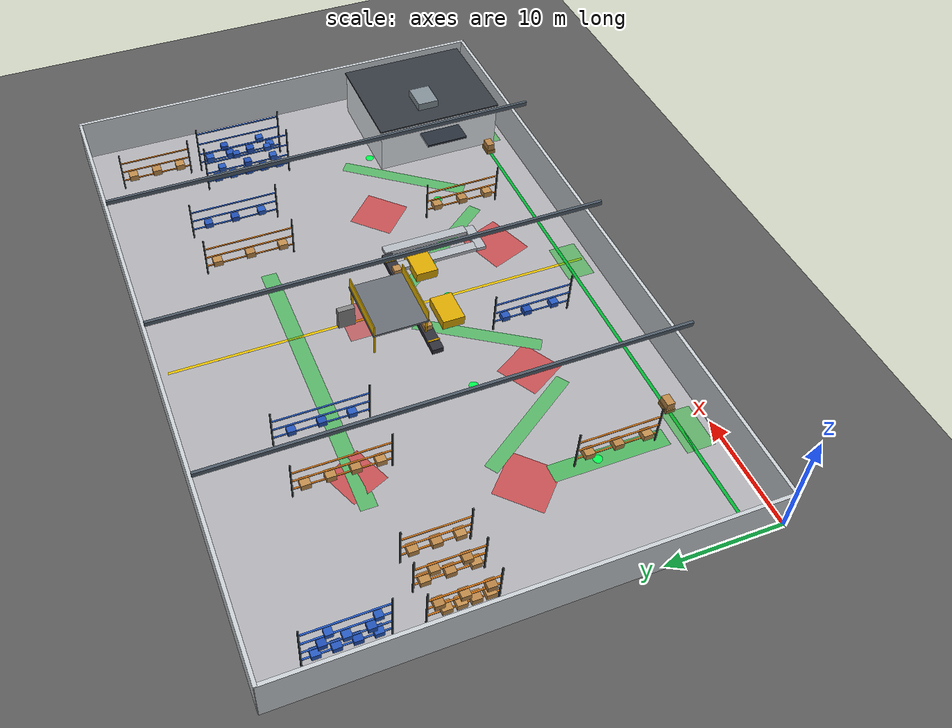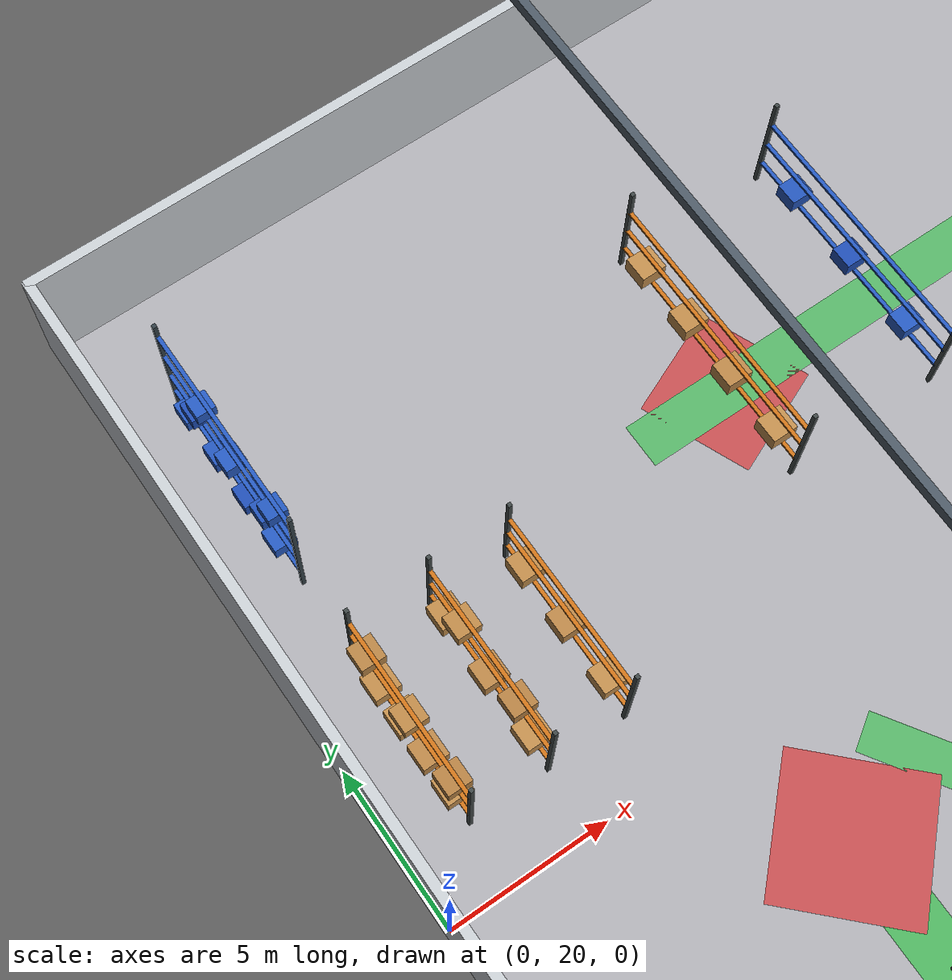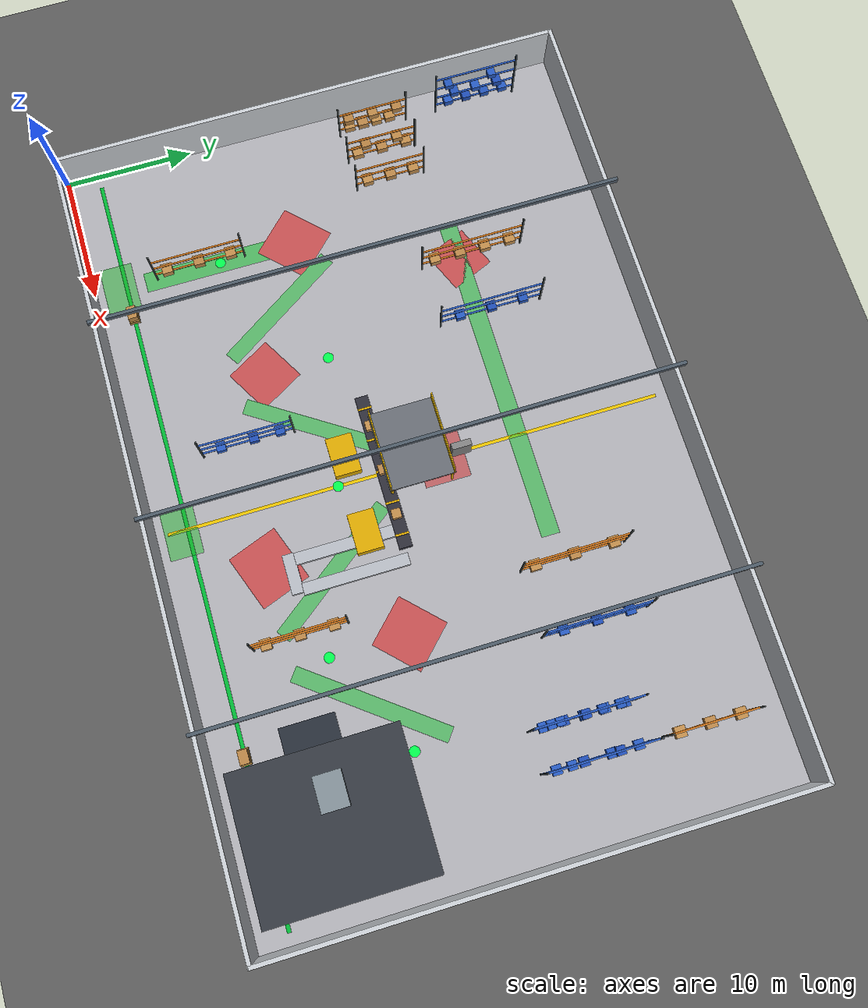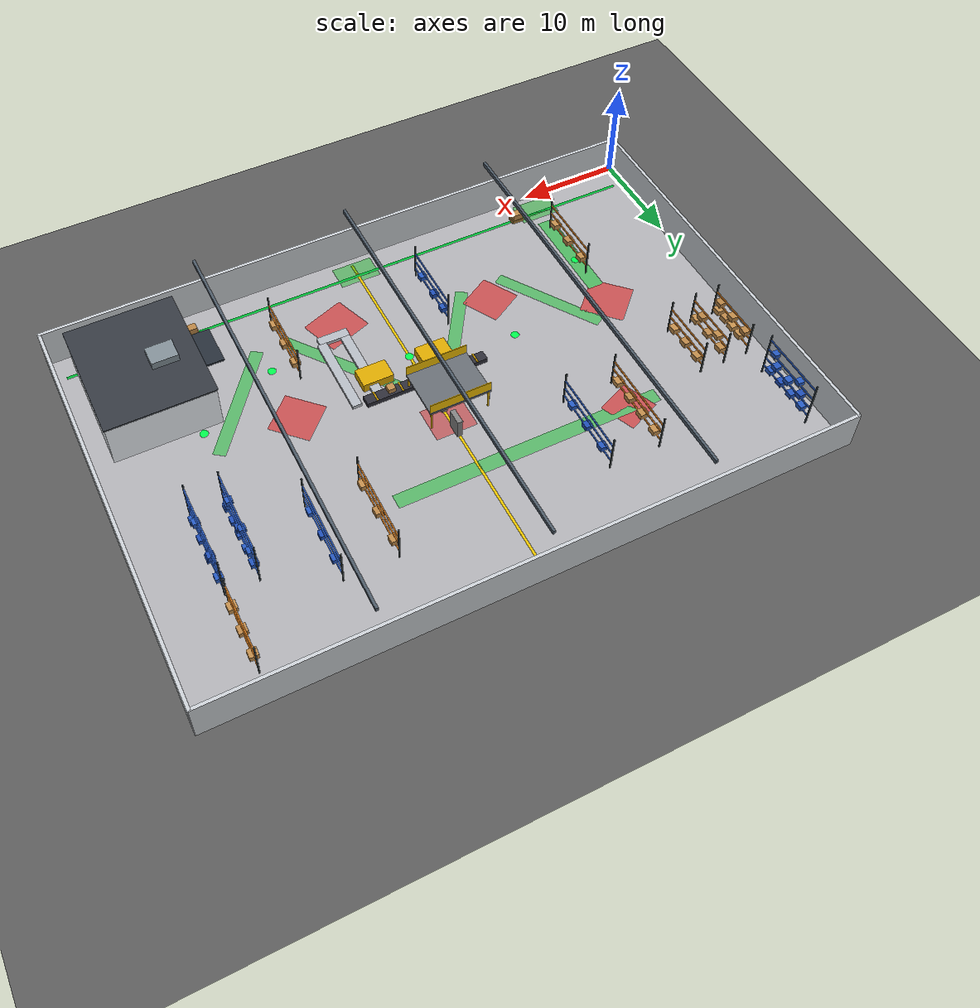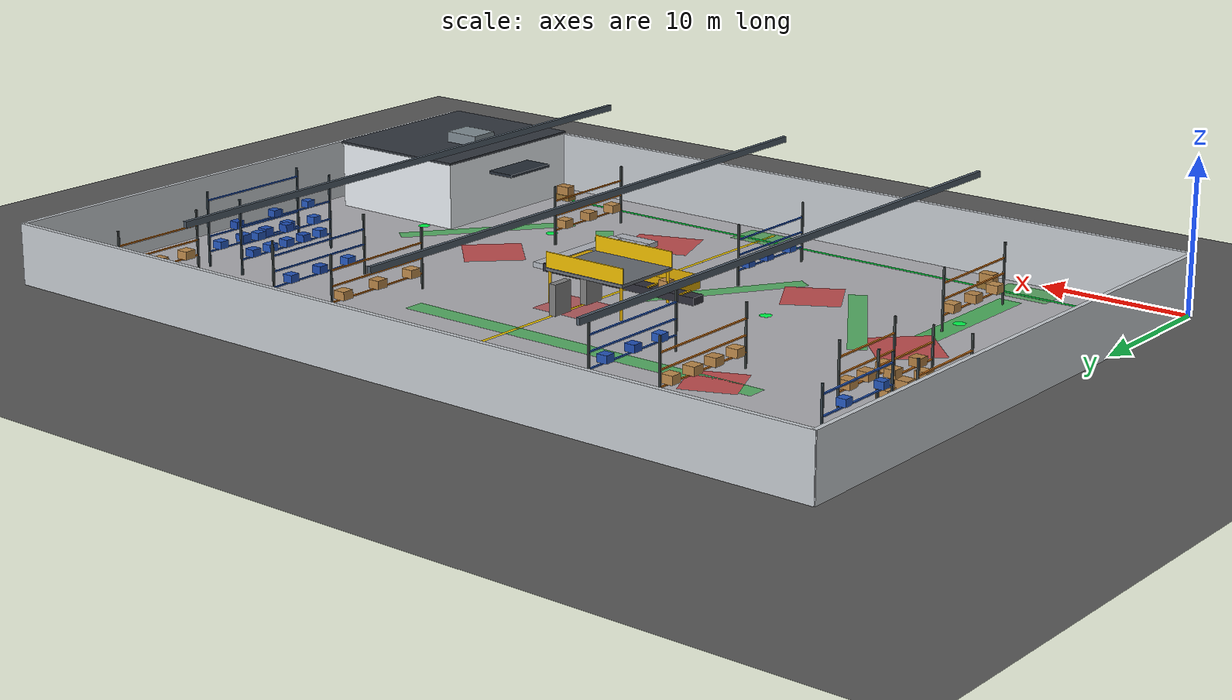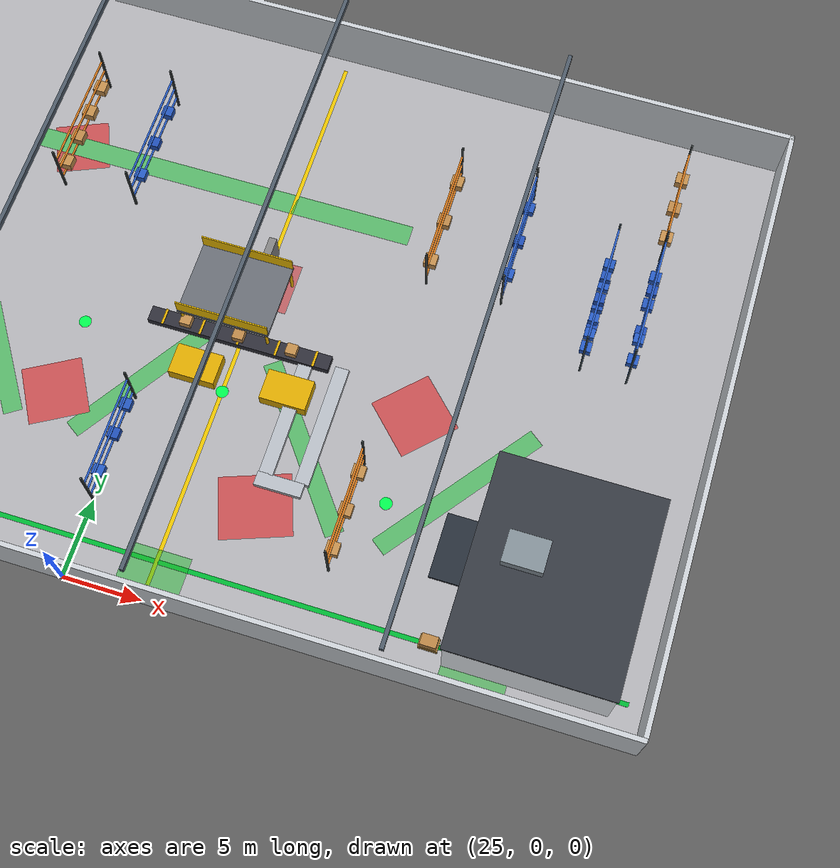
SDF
<?xml version="1.0" ?>
<sdf version="1.9">
  <world name="warehouse">

    <!-- Physics                                               -->
    <physics name="4ms" type="ignored">
      <max_step_size>0.004</max_step_size>
      <real_time_factor>1.0</real_time_factor>
    </physics>

    <!-- Plugins                                               -->
    <plugin filename="gz-sim-physics-system"        name="gz::sim::systems::Physics"/>
    <plugin filename="gz-sim-user-commands-system"  name="gz::sim::systems::UserCommands"/>
    <plugin filename="gz-sim-scene-broadcaster-system" name="gz::sim::systems::SceneBroadcaster"/>
    <plugin filename="gz-sim-sensors-system"        name="gz::sim::systems::Sensors">
      <render_engine>ogre2</render_engine>
    </plugin>
    <plugin filename="gz-sim-contact-system"        name="gz::sim::systems::Contact"/>

    <!-- Lighting — Industrial overhead                        -->
    <light type="directional" name="sun">
      <cast_shadows>true</cast_shadows>
      <pose>0 0 30 0 0.4 0</pose>
      <diffuse>0.9 0.9 0.85 1</diffuse>
      <specular>0.3 0.3 0.3 1</specular>
      <direction>-0.3 0.1 -0.95</direction>
    </light>
    <!-- Secondary fill light -->
    <light type="directional" name="fill_light">
      <cast_shadows>false</cast_shadows>
      <pose>0 0 20 0 0 0</pose>
      <diffuse>0.4 0.4 0.5 1</diffuse>
      <specular>0.0 0.0 0.0 1</specular>
      <direction>0.4 -0.2 -0.9</direction>
    </light>

    <!-- Camera — Isometric top-down like reference image      -->
    <gui fullscreen="0">
      <camera name="user_camera">
        <pose>30.0 -20.0 55.0 0 0.95 1.5708</pose>
        <view_controller>orbit</view_controller>
      </camera>
    </gui>

    <!-- GROUND PLANE  (60 m × 40 m)                          -->
    <model name="ground_plane">
      <static>true</static>
      <pose>0 0 0 0 0 0</pose>
      <link name="link">
        <collision name="collision">
          <geometry><plane><normal>0 0 1</normal><size>200 200</size></plane></geometry>
        </collision>
        <visual name="visual">
          <geometry><plane><normal>0 0 1</normal><size>200 200</size></plane></geometry>
          <material>
            <ambient>0.35 0.35 0.35 1</ambient>
            <diffuse>0.35 0.35 0.35 1</diffuse>
          </material>
        </visual>
      </link>
    </model>

    <!-- WAREHOUSE FLOOR  60 m × 40 m concrete                -->
    <!-- Origin: (30, 20, 0) → corners (0,0) to (60,40)       -->
    <model name="warehouse_floor">
      <static>true</static>
      <pose>30 20 0.001 0 0 0</pose>
      <link name="link">
        <collision name="collision">
          <geometry><box><size>60.0 40.0 0.002</size></box></geometry>
        </collision>
        <visual name="visual">
          <geometry><box><size>60.0 40.0 0.002</size></box></geometry>
          <material>
            <ambient>0.68 0.68 0.70 1</ambient>
            <diffuse>0.68 0.68 0.70 1</diffuse>
            <specular>0.15 0.15 0.15 1</specular>
          </material>
        </visual>
      </link>
    </model>

    <!-- WAREHOUSE WALLS  (4m tall)                           -->
    <!-- South wall y=0 -->
    <model name="wall_south">
      <static>true</static><pose>30 0 2.0 0 0 0</pose>
      <link name="link">
        <collision name="c"><geometry><box><size>60.2 0.3 4.0</size></box></geometry></collision>
        <visual name="v">
          <geometry><box><size>60.2 0.3 4.0</size></box></geometry>
          <material><ambient>0.78 0.80 0.82 1</ambient><diffuse>0.78 0.80 0.82 1</diffuse></material>
        </visual>
      </link>
    </model>
    <!-- North wall y=40 -->
    <model name="wall_north">
      <static>true</static><pose>30 40 2.0 0 0 0</pose>
      <link name="link">
        <collision name="c"><geometry><box><size>60.2 0.3 4.0</size></box></geometry></collision>
        <visual name="v">
          <geometry><box><size>60.2 0.3 4.0</size></box></geometry>
          <material><ambient>0.78 0.80 0.82 1</ambient><diffuse>0.78 0.80 0.82 1</diffuse></material>
        </visual>
      </link>
    </model>
    <!-- West wall x=0 -->
    <model name="wall_west">
      <static>true</static><pose>0 20 2.0 0 0 0</pose>
      <link name="link">
        <collision name="c"><geometry><box><size>0.3 40.2 4.0</size></box></geometry></collision>
        <visual name="v">
          <geometry><box><size>0.3 40.2 4.0</size></box></geometry>
          <material><ambient>0.78 0.80 0.82 1</ambient><diffuse>0.78 0.80 0.82 1</diffuse></material>
        </visual>
      </link>
    </model>
    <!-- East wall x=60 -->
    <model name="wall_east">
      <static>true</static><pose>60 20 2.0 0 0 0</pose>
      <link name="link">
        <collision name="c"><geometry><box><size>0.3 40.2 4.0</size></box></geometry></collision>
        <visual name="v">
          <geometry><box><size>0.3 40.2 4.0</size></box></geometry>
          <material><ambient>0.78 0.80 0.82 1</ambient><diffuse>0.78 0.80 0.82 1</diffuse></material>
        </visual>
      </link>
    </model>

    <!-- MACRO: RACK UPRIGHT (helper shape reused many times)  -->
    <!-- Upright post: 0.1×0.1×4m, steel gray                 -->

    <!-- ZONE A: LEFT ORANGE RACK BLOCK (x=1.5..10, y=22..38) -->
    <!-- 4-tier racks, orange cardboard box color             -->

    <!-- Rack A row 1 — uprights -->
    <model name="rack_A1_upright_l"><static>true</static><pose>2.0 22.0 2.0 0 0 0</pose>
      <link name="link"><collision name="c"><geometry><box><size>0.12 0.12 4.0</size></box></geometry></collision>
        <visual name="v"><geometry><box><size>0.12 0.12 4.0</size></box></geometry>
          <material><ambient>0.25 0.28 0.28 1</ambient><diffuse>0.25 0.28 0.28 1</diffuse></material></visual></link></model>
    <model name="rack_A1_upright_r"><static>true</static><pose>2.0 27.5 2.0 0 0 0</pose>
      <link name="link"><collision name="c"><geometry><box><size>0.12 0.12 4.0</size></box></geometry></collision>
        <visual name="v"><geometry><box><size>0.12 0.12 4.0</size></box></geometry>
          <material><ambient>0.25 0.28 0.28 1</ambient><diffuse>0.25 0.28 0.28 1</diffuse></material></visual></link></model>
    <!-- Horizontal beam tier 1 (h=1.0) -->
    <model name="rack_A1_beam1"><static>true</static><pose>2.0 24.75 1.0 0 0 0</pose>
      <link name="link"><collision name="c"><geometry><box><size>0.12 5.5 0.08</size></box></geometry></collision>
        <visual name="v"><geometry><box><size>0.12 5.5 0.08</size></box></geometry>
          <material><ambient>0.8 0.45 0.1 1</ambient><diffuse>0.8 0.45 0.1 1</diffuse></material></visual></link></model>
    <!-- Horizontal beam tier 2 (h=2.0) -->
    <model name="rack_A1_beam2"><static>true</static><pose>2.0 24.75 2.0 0 0 0</pose>
      <link name="link"><collision name="c"><geometry><box><size>0.12 5.5 0.08</size></box></geometry></collision>
        <visual name="v"><geometry><box><size>0.12 5.5 0.08</size></box></geometry>
          <material><ambient>0.8 0.45 0.1 1</ambient><diffuse>0.8 0.45 0.1 1</diffuse></material></visual></link></model>
    <!-- Horizontal beam tier 3 (h=3.0) -->
    <model name="rack_A1_beam3"><static>true</static><pose>2.0 24.75 3.0 0 0 0</pose>
      <link name="link"><collision name="c"><geometry><box><size>0.12 5.5 0.08</size></box></geometry></collision>
        <visual name="v"><geometry><box><size>0.12 5.5 0.08</size></box></geometry>
          <material><ambient>0.8 0.45 0.1 1</ambient><diffuse>0.8 0.45 0.1 1</diffuse></material></visual></link></model>

    <!-- Boxes on rack A1 tier 1 -->
    <model name="box_A1_t1_1"><static>true</static><pose>2.0 22.8 1.3 0 0 0</pose>
      <link name="link"><collision name="c"><geometry><box><size>0.8 0.8 0.55</size></box></geometry></collision>
        <visual name="v"><geometry><box><size>0.8 0.8 0.55</size></box></geometry>
          <material><ambient>0.75 0.55 0.3 1</ambient><diffuse>0.75 0.55 0.3 1</diffuse></material></visual></link></model>
    <model name="box_A1_t1_2"><static>true</static><pose>2.0 23.9 1.3 0 0 0</pose>
      <link name="link"><collision name="c"><geometry><box><size>0.8 0.8 0.55</size></box></geometry></collision>
        <visual name="v"><geometry><box><size>0.8 0.8 0.55</size></box></geometry>
          <material><ambient>0.72 0.52 0.28 1</ambient><diffuse>0.72 0.52 0.28 1</diffuse></material></visual></link></model>
    <model name="box_A1_t1_3"><static>true</static><pose>2.0 25.0 1.3 0 0 0</pose>
      <link name="link"><collision name="c"><geometry><box><size>0.8 0.8 0.55</size></box></geometry></collision>
        <visual name="v"><geometry><box><size>0.8 0.8 0.55</size></box></geometry>
          <material><ambient>0.76 0.56 0.3 1</ambient><diffuse>0.76 0.56 0.3 1</diffuse></material></visual></link></model>
    <model name="box_A1_t1_4"><static>true</static><pose>2.0 26.1 1.3 0 0 0</pose>
      <link name="link"><collision name="c"><geometry><box><size>0.8 0.8 0.55</size></box></geometry></collision>
        <visual name="v"><geometry><box><size>0.8 0.8 0.55</size></box></geometry>
          <material><ambient>0.74 0.54 0.29 1</ambient><diffuse>0.74 0.54 0.29 1</diffuse></material></visual></link></model>
    <!-- Boxes tier 2 -->
    <model name="box_A1_t2_1"><static>true</static><pose>2.0 22.8 2.3 0 0 0</pose>
      <link name="link"><collision name="c"><geometry><box><size>0.75 0.75 0.5</size></box></geometry></collision>
        <visual name="v"><geometry><box><size>0.75 0.75 0.5</size></box></geometry>
          <material><ambient>0.70 0.50 0.26 1</ambient><diffuse>0.70 0.50 0.26 1</diffuse></material></visual></link></model>
    <model name="box_A1_t2_2"><static>true</static><pose>2.0 24.75 2.3 0 0 0</pose>
      <link name="link"><collision name="c"><geometry><box><size>0.75 0.75 0.5</size></box></geometry></collision>
        <visual name="v"><geometry><box><size>0.75 0.75 0.5</size></box></geometry>
          <material><ambient>0.73 0.53 0.28 1</ambient><diffuse>0.73 0.53 0.28 1</diffuse></material></visual></link></model>
    <model name="box_A1_t2_3"><static>true</static><pose>2.0 26.7 2.3 0 0 0</pose>
      <link name="link"><collision name="c"><geometry><box><size>0.75 0.75 0.5</size></box></geometry></collision>
        <visual name="v"><geometry><box><size>0.75 0.75 0.5</size></box></geometry>
          <material><ambient>0.71 0.51 0.27 1</ambient><diffuse>0.71 0.51 0.27 1</diffuse></material></visual></link></model>

    <!-- Rack A row 2 (deeper, x=4.0) -->
    <model name="rack_A2_upright_l"><static>true</static><pose>4.5 22.0 2.0 0 0 0</pose>
      <link name="link"><collision name="c"><geometry><box><size>0.12 0.12 4.0</size></box></geometry></collision>
        <visual name="v"><geometry><box><size>0.12 0.12 4.0</size></box></geometry>
          <material><ambient>0.25 0.28 0.28 1</ambient><diffuse>0.25 0.28 0.28 1</diffuse></material></visual></link></model>
    <model name="rack_A2_upright_r"><static>true</static><pose>4.5 27.5 2.0 0 0 0</pose>
      <link name="link"><collision name="c"><geometry><box><size>0.12 0.12 4.0</size></box></geometry></collision>
        <visual name="v"><geometry><box><size>0.12 0.12 4.0</size></box></geometry>
          <material><ambient>0.25 0.28 0.28 1</ambient><diffuse>0.25 0.28 0.28 1</diffuse></material></visual></link></model>
    <model name="rack_A2_beam1"><static>true</static><pose>4.5 24.75 1.0 0 0 0</pose>
      <link name="link"><collision name="c"><geometry><box><size>0.12 5.5 0.08</size></box></geometry></collision>
        <visual name="v"><geometry><box><size>0.12 5.5 0.08</size></box></geometry>
          <material><ambient>0.8 0.45 0.1 1</ambient><diffuse>0.8 0.45 0.1 1</diffuse></material></visual></link></model>
    <model name="rack_A2_beam2"><static>true</static><pose>4.5 24.75 2.0 0 0 0</pose>
      <link name="link"><collision name="c"><geometry><box><size>0.12 5.5 0.08</size></box></geometry></collision>
        <visual name="v"><geometry><box><size>0.12 5.5 0.08</size></box></geometry>
          <material><ambient>0.8 0.45 0.1 1</ambient><diffuse>0.8 0.45 0.1 1</diffuse></material></visual></link></model>
    <model name="rack_A2_beam3"><static>true</static><pose>4.5 24.75 3.0 0 0 0</pose>
      <link name="link"><collision name="c"><geometry><box><size>0.12 5.5 0.08</size></box></geometry></collision>
        <visual name="v"><geometry><box><size>0.12 5.5 0.08</size></box></geometry>
          <material><ambient>0.8 0.45 0.1 1</ambient><diffuse>0.8 0.45 0.1 1</diffuse></material></visual></link></model>
    <!-- Boxes rack A2 -->
    <model name="box_A2_t1_1"><static>true</static><pose>4.5 22.8 1.3 0 0 0</pose>
      <link name="link"><collision name="c"><geometry><box><size>0.8 0.8 0.55</size></box></geometry></collision>
        <visual name="v"><geometry><box><size>0.8 0.8 0.55</size></box></geometry>
          <material><ambient>0.75 0.55 0.30 1</ambient><diffuse>0.75 0.55 0.30 1</diffuse></material></visual></link></model>
    <model name="box_A2_t1_2"><static>true</static><pose>4.5 24.75 1.3 0 0 0</pose>
      <link name="link"><collision name="c"><geometry><box><size>0.8 0.8 0.55</size></box></geometry></collision>
        <visual name="v"><geometry><box><size>0.8 0.8 0.55</size></box></geometry>
          <material><ambient>0.72 0.52 0.28 1</ambient><diffuse>0.72 0.52 0.28 1</diffuse></material></visual></link></model>
    <model name="box_A2_t1_3"><static>true</static><pose>4.5 26.7 1.3 0 0 0</pose>
      <link name="link"><collision name="c"><geometry><box><size>0.8 0.8 0.55</size></box></geometry></collision>
        <visual name="v"><geometry><box><size>0.8 0.8 0.55</size></box></geometry>
          <material><ambient>0.74 0.54 0.29 1</ambient><diffuse>0.74 0.54 0.29 1</diffuse></material></visual></link></model>
    <model name="box_A2_t2_1"><static>true</static><pose>4.5 23.5 2.3 0 0 0</pose>
      <link name="link"><collision name="c"><geometry><box><size>0.75 0.75 0.5</size></box></geometry></collision>
        <visual name="v"><geometry><box><size>0.75 0.75 0.5</size></box></geometry>
          <material><ambient>0.70 0.50 0.26 1</ambient><diffuse>0.70 0.50 0.26 1</diffuse></material></visual></link></model>
    <model name="box_A2_t2_2"><static>true</static><pose>4.5 26.0 2.3 0 0 0</pose>
      <link name="link"><collision name="c"><geometry><box><size>0.75 0.75 0.5</size></box></geometry></collision>
        <visual name="v"><geometry><box><size>0.75 0.75 0.5</size></box></geometry>
          <material><ambient>0.73 0.53 0.28 1</ambient><diffuse>0.73 0.53 0.28 1</diffuse></material></visual></link></model>

    <!-- Rack A row 3 (x=7.0) -->
    <model name="rack_A3_upright_l"><static>true</static><pose>7.0 22.0 2.0 0 0 0</pose>
      <link name="link"><collision name="c"><geometry><box><size>0.12 0.12 4.0</size></box></geometry></collision>
        <visual name="v"><geometry><box><size>0.12 0.12 4.0</size></box></geometry>
          <material><ambient>0.25 0.28 0.28 1</ambient><diffuse>0.25 0.28 0.28 1</diffuse></material></visual></link></model>
    <model name="rack_A3_upright_r"><static>true</static><pose>7.0 27.5 2.0 0 0 0</pose>
      <link name="link"><collision name="c"><geometry><box><size>0.12 0.12 4.0</size></box></geometry></collision>
        <visual name="v"><geometry><box><size>0.12 0.12 4.0</size></box></geometry>
          <material><ambient>0.25 0.28 0.28 1</ambient><diffuse>0.25 0.28 0.28 1</diffuse></material></visual></link></model>
    <model name="rack_A3_beam1"><static>true</static><pose>7.0 24.75 1.0 0 0 0</pose>
      <link name="link"><collision name="c"><geometry><box><size>0.12 5.5 0.08</size></box></geometry></collision>
        <visual name="v"><geometry><box><size>0.12 5.5 0.08</size></box></geometry>
          <material><ambient>0.8 0.45 0.1 1</ambient><diffuse>0.8 0.45 0.1 1</diffuse></material></visual></link></model>
    <model name="rack_A3_beam2"><static>true</static><pose>7.0 24.75 2.0 0 0 0</pose>
      <link name="link"><collision name="c"><geometry><box><size>0.12 5.5 0.08</size></box></geometry></collision>
        <visual name="v"><geometry><box><size>0.12 5.5 0.08</size></box></geometry>
          <material><ambient>0.8 0.45 0.1 1</ambient><diffuse>0.8 0.45 0.1 1</diffuse></material></visual></link></model>
    <model name="rack_A3_beam3"><static>true</static><pose>7.0 24.75 3.0 0 0 0</pose>
      <link name="link"><collision name="c"><geometry><box><size>0.12 5.5 0.08</size></box></geometry></collision>
        <visual name="v"><geometry><box><size>0.12 5.5 0.08</size></box></geometry>
          <material><ambient>0.8 0.45 0.1 1</ambient><diffuse>0.8 0.45 0.1 1</diffuse></material></visual></link></model>
    <!-- Boxes rack A3 -->
    <model name="box_A3_t1_1"><static>true</static><pose>7.0 22.9 1.3 0 0 0</pose>
      <link name="link"><collision name="c"><geometry><box><size>0.8 0.8 0.55</size></box></geometry></collision>
        <visual name="v"><geometry><box><size>0.8 0.8 0.55</size></box></geometry>
          <material><ambient>0.75 0.55 0.3 1</ambient><diffuse>0.75 0.55 0.3 1</diffuse></material></visual></link></model>
    <model name="box_A3_t1_2"><static>true</static><pose>7.0 24.75 1.3 0 0 0</pose>
      <link name="link"><collision name="c"><geometry><box><size>0.8 0.8 0.55</size></box></geometry></collision>
        <visual name="v"><geometry><box><size>0.8 0.8 0.55</size></box></geometry>
          <material><ambient>0.72 0.52 0.28 1</ambient><diffuse>0.72 0.52 0.28 1</diffuse></material></visual></link></model>
    <model name="box_A3_t1_3"><static>true</static><pose>7.0 26.6 1.3 0 0 0</pose>
      <link name="link"><collision name="c"><geometry><box><size>0.8 0.8 0.55</size></box></geometry></collision>
        <visual name="v"><geometry><box><size>0.8 0.8 0.55</size></box></geometry>
          <material><ambient>0.74 0.54 0.29 1</ambient><diffuse>0.74 0.54 0.29 1</diffuse></material></visual></link></model>

    <!-- ZONE A lower sub-rack (y=30..37) — tall blue storage unit -->
    <model name="rack_Ab1_upright_l"><static>true</static><pose>2.0 30.0 2.5 0 0 0</pose>
      <link name="link"><collision name="c"><geometry><box><size>0.12 0.12 5.0</size></box></geometry></collision>
        <visual name="v"><geometry><box><size>0.12 0.12 5.0</size></box></geometry>
          <material><ambient>0.2 0.25 0.28 1</ambient><diffuse>0.2 0.25 0.28 1</diffuse></material></visual></link></model>
    <model name="rack_Ab1_upright_r"><static>true</static><pose>2.0 36.5 2.5 0 0 0</pose>
      <link name="link"><collision name="c"><geometry><box><size>0.12 0.12 5.0</size></box></geometry></collision>
        <visual name="v"><geometry><box><size>0.12 0.12 5.0</size></box></geometry>
          <material><ambient>0.2 0.25 0.28 1</ambient><diffuse>0.2 0.25 0.28 1</diffuse></material></visual></link></model>
    <model name="rack_Ab1_beam1"><static>true</static><pose>2.0 33.25 1.0 0 0 0</pose>
      <link name="link"><collision name="c"><geometry><box><size>0.12 6.5 0.08</size></box></geometry></collision>
        <visual name="v"><geometry><box><size>0.12 6.5 0.08</size></box></geometry>
          <material><ambient>0.15 0.35 0.75 1</ambient><diffuse>0.15 0.35 0.75 1</diffuse></material></visual></link></model>
    <model name="rack_Ab1_beam2"><static>true</static><pose>2.0 33.25 2.0 0 0 0</pose>
      <link name="link"><collision name="c"><geometry><box><size>0.12 6.5 0.08</size></box></geometry></collision>
        <visual name="v"><geometry><box><size>0.12 6.5 0.08</size></box></geometry>
          <material><ambient>0.15 0.35 0.75 1</ambient><diffuse>0.15 0.35 0.75 1</diffuse></material></visual></link></model>
    <model name="rack_Ab1_beam3"><static>true</static><pose>2.0 33.25 3.2 0 0 0</pose>
      <link name="link"><collision name="c"><geometry><box><size>0.12 6.5 0.08</size></box></geometry></collision>
        <visual name="v"><geometry><box><size>0.12 6.5 0.08</size></box></geometry>
          <material><ambient>0.15 0.35 0.75 1</ambient><diffuse>0.15 0.35 0.75 1</diffuse></material></visual></link></model>
    <model name="rack_Ab1_beam4"><static>true</static><pose>2.0 33.25 4.4 0 0 0</pose>
      <link name="link"><collision name="c"><geometry><box><size>0.12 6.5 0.08</size></box></geometry></collision>
        <visual name="v"><geometry><box><size>0.12 6.5 0.08</size></box></geometry>
          <material><ambient>0.15 0.35 0.75 1</ambient><diffuse>0.15 0.35 0.75 1</diffuse></material></visual></link></model>
    <!-- Blue boxes on tall rack -->
    <model name="box_Ab1_t1_1"><static>true</static><pose>2.0 31.0 1.3 0 0 0</pose>
      <link name="link"><collision name="c"><geometry><box><size>0.7 0.7 0.5</size></box></geometry></collision>
        <visual name="v"><geometry><box><size>0.7 0.7 0.5</size></box></geometry>
          <material><ambient>0.15 0.35 0.75 1</ambient><diffuse>0.15 0.35 0.75 1</diffuse></material></visual></link></model>
    <model name="box_Ab1_t1_2"><static>true</static><pose>2.0 32.5 1.3 0 0 0</pose>
      <link name="link"><collision name="c"><geometry><box><size>0.7 0.7 0.5</size></box></geometry></collision>
        <visual name="v"><geometry><box><size>0.7 0.7 0.5</size></box></geometry>
          <material><ambient>0.12 0.30 0.70 1</ambient><diffuse>0.12 0.30 0.70 1</diffuse></material></visual></link></model>
    <model name="box_Ab1_t1_3"><static>true</static><pose>2.0 34.0 1.3 0 0 0</pose>
      <link name="link"><collision name="c"><geometry><box><size>0.7 0.7 0.5</size></box></geometry></collision>
        <visual name="v"><geometry><box><size>0.7 0.7 0.5</size></box></geometry>
          <material><ambient>0.14 0.33 0.72 1</ambient><diffuse>0.14 0.33 0.72 1</diffuse></material></visual></link></model>
    <model name="box_Ab1_t1_4"><static>true</static><pose>2.0 35.5 1.3 0 0 0</pose>
      <link name="link"><collision name="c"><geometry><box><size>0.7 0.7 0.5</size></box></geometry></collision>
        <visual name="v"><geometry><box><size>0.7 0.7 0.5</size></box></geometry>
          <material><ambient>0.15 0.35 0.75 1</ambient><diffuse>0.15 0.35 0.75 1</diffuse></material></visual></link></model>
    <model name="box_Ab1_t2_1"><static>true</static><pose>2.0 31.5 2.3 0 0 0</pose>
      <link name="link"><collision name="c"><geometry><box><size>0.65 0.65 0.5</size></box></geometry></collision>
        <visual name="v"><geometry><box><size>0.65 0.65 0.5</size></box></geometry>
          <material><ambient>0.13 0.32 0.71 1</ambient><diffuse>0.13 0.32 0.71 1</diffuse></material></visual></link></model>
    <model name="box_Ab1_t2_2"><static>true</static><pose>2.0 33.25 2.3 0 0 0</pose>
      <link name="link"><collision name="c"><geometry><box><size>0.65 0.65 0.5</size></box></geometry></collision>
        <visual name="v"><geometry><box><size>0.65 0.65 0.5</size></box></geometry>
          <material><ambient>0.15 0.35 0.75 1</ambient><diffuse>0.15 0.35 0.75 1</diffuse></material></visual></link></model>
    <model name="box_Ab1_t2_3"><static>true</static><pose>2.0 35.0 2.3 0 0 0</pose>
      <link name="link"><collision name="c"><geometry><box><size>0.65 0.65 0.5</size></box></geometry></collision>
        <visual name="v"><geometry><box><size>0.65 0.65 0.5</size></box></geometry>
          <material><ambient>0.12 0.30 0.70 1</ambient><diffuse>0.12 0.30 0.70 1</diffuse></material></visual></link></model>
    <model name="box_Ab1_t3_1"><static>true</static><pose>2.0 31.0 3.5 0 0 0</pose>
      <link name="link"><collision name="c"><geometry><box><size>0.6 0.6 0.45</size></box></geometry></collision>
        <visual name="v"><geometry><box><size>0.6 0.6 0.45</size></box></geometry>
          <material><ambient>0.14 0.34 0.73 1</ambient><diffuse>0.14 0.34 0.73 1</diffuse></material></visual></link></model>
    <model name="box_Ab1_t3_2"><static>true</static><pose>2.0 34.5 3.5 0 0 0</pose>
      <link name="link"><collision name="c"><geometry><box><size>0.6 0.6 0.45</size></box></geometry></collision>
        <visual name="v"><geometry><box><size>0.6 0.6 0.45</size></box></geometry>
          <material><ambient>0.15 0.35 0.75 1</ambient><diffuse>0.15 0.35 0.75 1</diffuse></material></visual></link></model>

    <!-- ZONE B: RIGHT BLUE RACK BLOCK (x=50..58, y=22..38)  -->
    <!-- Rack B1 (x=51) -->
    <model name="rack_B1_upright_l"><static>true</static><pose>51.0 22.0 2.5 0 0 0</pose>
      <link name="link"><collision name="c"><geometry><box><size>0.12 0.12 5.0</size></box></geometry></collision>
        <visual name="v"><geometry><box><size>0.12 0.12 5.0</size></box></geometry>
          <material><ambient>0.2 0.25 0.28 1</ambient><diffuse>0.2 0.25 0.28 1</diffuse></material></visual></link></model>
    <model name="rack_B1_upright_r"><static>true</static><pose>51.0 30.0 2.5 0 0 0</pose>
      <link name="link"><collision name="c"><geometry><box><size>0.12 0.12 5.0</size></box></geometry></collision>
        <visual name="v"><geometry><box><size>0.12 0.12 5.0</size></box></geometry>
          <material><ambient>0.2 0.25 0.28 1</ambient><diffuse>0.2 0.25 0.28 1</diffuse></material></visual></link></model>
    <model name="rack_B1_beam1"><static>true</static><pose>51.0 26.0 1.0 0 0 0</pose>
      <link name="link"><collision name="c"><geometry><box><size>0.12 8.0 0.08</size></box></geometry></collision>
        <visual name="v"><geometry><box><size>0.12 8.0 0.08</size></box></geometry>
          <material><ambient>0.15 0.35 0.75 1</ambient><diffuse>0.15 0.35 0.75 1</diffuse></material></visual></link></model>
    <model name="rack_B1_beam2"><static>true</static><pose>51.0 26.0 2.0 0 0 0</pose>
      <link name="link"><collision name="c"><geometry><box><size>0.12 8.0 0.08</size></box></geometry></collision>
        <visual name="v"><geometry><box><size>0.12 8.0 0.08</size></box></geometry>
          <material><ambient>0.15 0.35 0.75 1</ambient><diffuse>0.15 0.35 0.75 1</diffuse></material></visual></link></model>
    <model name="rack_B1_beam3"><static>true</static><pose>51.0 26.0 3.2 0 0 0</pose>
      <link name="link"><collision name="c"><geometry><box><size>0.12 8.0 0.08</size></box></geometry></collision>
        <visual name="v"><geometry><box><size>0.12 8.0 0.08</size></box></geometry>
          <material><ambient>0.15 0.35 0.75 1</ambient><diffuse>0.15 0.35 0.75 1</diffuse></material></visual></link></model>
    <model name="rack_B1_beam4"><static>true</static><pose>51.0 26.0 4.4 0 0 0</pose>
      <link name="link"><collision name="c"><geometry><box><size>0.12 8.0 0.08</size></box></geometry></collision>
        <visual name="v"><geometry><box><size>0.12 8.0 0.08</size></box></geometry>
          <material><ambient>0.15 0.35 0.75 1</ambient><diffuse>0.15 0.35 0.75 1</diffuse></material></visual></link></model>
    <!-- Blue boxes on B1 -->
    <model name="box_B1_t1_1"><static>true</static><pose>51.0 23.0 1.3 0 0 0</pose>
      <link name="link"><collision name="c"><geometry><box><size>0.7 0.7 0.5</size></box></geometry></collision>
        <visual name="v"><geometry><box><size>0.7 0.7 0.5</size></box></geometry>
          <material><ambient>0.15 0.35 0.75 1</ambient><diffuse>0.15 0.35 0.75 1</diffuse></material></visual></link></model>
    <model name="box_B1_t1_2"><static>true</static><pose>51.0 24.5 1.3 0 0 0</pose>
      <link name="link"><collision name="c"><geometry><box><size>0.7 0.7 0.5</size></box></geometry></collision>
        <visual name="v"><geometry><box><size>0.7 0.7 0.5</size></box></geometry>
          <material><ambient>0.12 0.30 0.70 1</ambient><diffuse>0.12 0.30 0.70 1</diffuse></material></visual></link></model>
    <model name="box_B1_t1_3"><static>true</static><pose>51.0 26.0 1.3 0 0 0</pose>
      <link name="link"><collision name="c"><geometry><box><size>0.7 0.7 0.5</size></box></geometry></collision>
        <visual name="v"><geometry><box><size>0.7 0.7 0.5</size></box></geometry>
          <material><ambient>0.14 0.33 0.72 1</ambient><diffuse>0.14 0.33 0.72 1</diffuse></material></visual></link></model>
    <model name="box_B1_t1_4"><static>true</static><pose>51.0 27.5 1.3 0 0 0</pose>
      <link name="link"><collision name="c"><geometry><box><size>0.7 0.7 0.5</size></box></geometry></collision>
        <visual name="v"><geometry><box><size>0.7 0.7 0.5</size></box></geometry>
          <material><ambient>0.15 0.35 0.75 1</ambient><diffuse>0.15 0.35 0.75 1</diffuse></material></visual></link></model>
    <model name="box_B1_t1_5"><static>true</static><pose>51.0 29.0 1.3 0 0 0</pose>
      <link name="link"><collision name="c"><geometry><box><size>0.7 0.7 0.5</size></box></geometry></collision>
        <visual name="v"><geometry><box><size>0.7 0.7 0.5</size></box></geometry>
          <material><ambient>0.13 0.32 0.71 1</ambient><diffuse>0.13 0.32 0.71 1</diffuse></material></visual></link></model>
    <model name="box_B1_t2_1"><static>true</static><pose>51.0 23.5 2.3 0 0 0</pose>
      <link name="link"><collision name="c"><geometry><box><size>0.65 0.65 0.5</size></box></geometry></collision>
        <visual name="v"><geometry><box><size>0.65 0.65 0.5</size></box></geometry>
          <material><ambient>0.15 0.35 0.75 1</ambient><diffuse>0.15 0.35 0.75 1</diffuse></material></visual></link></model>
    <model name="box_B1_t2_2"><static>true</static><pose>51.0 26.0 2.3 0 0 0</pose>
      <link name="link"><collision name="c"><geometry><box><size>0.65 0.65 0.5</size></box></geometry></collision>
        <visual name="v"><geometry><box><size>0.65 0.65 0.5</size></box></geometry>
          <material><ambient>0.12 0.30 0.70 1</ambient><diffuse>0.12 0.30 0.70 1</diffuse></material></visual></link></model>
    <model name="box_B1_t2_3"><static>true</static><pose>51.0 28.5 2.3 0 0 0</pose>
      <link name="link"><collision name="c"><geometry><box><size>0.65 0.65 0.5</size></box></geometry></collision>
        <visual name="v"><geometry><box><size>0.65 0.65 0.5</size></box></geometry>
          <material><ambient>0.14 0.34 0.73 1</ambient><diffuse>0.14 0.34 0.73 1</diffuse></material></visual></link></model>
    <model name="box_B1_t3_1"><static>true</static><pose>51.0 24.0 3.5 0 0 0</pose>
      <link name="link"><collision name="c"><geometry><box><size>0.6 0.6 0.45</size></box></geometry></collision>
        <visual name="v"><geometry><box><size>0.6 0.6 0.45</size></box></geometry>
          <material><ambient>0.15 0.35 0.75 1</ambient><diffuse>0.15 0.35 0.75 1</diffuse></material></visual></link></model>
    <model name="box_B1_t3_2"><static>true</static><pose>51.0 27.0 3.5 0 0 0</pose>
      <link name="link"><collision name="c"><geometry><box><size>0.6 0.6 0.45</size></box></geometry></collision>
        <visual name="v"><geometry><box><size>0.6 0.6 0.45</size></box></geometry>
          <material><ambient>0.13 0.32 0.71 1</ambient><diffuse>0.13 0.32 0.71 1</diffuse></material></visual></link></model>

    <!-- Rack B2 (x=54) -->
    <model name="rack_B2_upright_l"><static>true</static><pose>54.0 22.0 2.5 0 0 0</pose>
      <link name="link"><collision name="c"><geometry><box><size>0.12 0.12 5.0</size></box></geometry></collision>
        <visual name="v"><geometry><box><size>0.12 0.12 5.0</size></box></geometry>
          <material><ambient>0.2 0.25 0.28 1</ambient><diffuse>0.2 0.25 0.28 1</diffuse></material></visual></link></model>
    <model name="rack_B2_upright_r"><static>true</static><pose>54.0 30.0 2.5 0 0 0</pose>
      <link name="link"><collision name="c"><geometry><box><size>0.12 0.12 5.0</size></box></geometry></collision>
        <visual name="v"><geometry><box><size>0.12 0.12 5.0</size></box></geometry>
          <material><ambient>0.2 0.25 0.28 1</ambient><diffuse>0.2 0.25 0.28 1</diffuse></material></visual></link></model>
    <model name="rack_B2_beam1"><static>true</static><pose>54.0 26.0 1.0 0 0 0</pose>
      <link name="link"><collision name="c"><geometry><box><size>0.12 8.0 0.08</size></box></geometry></collision>
        <visual name="v"><geometry><box><size>0.12 8.0 0.08</size></box></geometry>
          <material><ambient>0.15 0.35 0.75 1</ambient><diffuse>0.15 0.35 0.75 1</diffuse></material></visual></link></model>
    <model name="rack_B2_beam2"><static>true</static><pose>54.0 26.0 2.0 0 0 0</pose>
      <link name="link"><collision name="c"><geometry><box><size>0.12 8.0 0.08</size></box></geometry></collision>
        <visual name="v"><geometry><box><size>0.12 8.0 0.08</size></box></geometry>
          <material><ambient>0.15 0.35 0.75 1</ambient><diffuse>0.15 0.35 0.75 1</diffuse></material></visual></link></model>
    <model name="rack_B2_beam3"><static>true</static><pose>54.0 26.0 3.2 0 0 0</pose>
      <link name="link"><collision name="c"><geometry><box><size>0.12 8.0 0.08</size></box></geometry></collision>
        <visual name="v"><geometry><box><size>0.12 8.0 0.08</size></box></geometry>
          <material><ambient>0.15 0.35 0.75 1</ambient><diffuse>0.15 0.35 0.75 1</diffuse></material></visual></link></model>
    <model name="rack_B2_beam4"><static>true</static><pose>54.0 26.0 4.4 0 0 0</pose>
      <link name="link"><collision name="c"><geometry><box><size>0.12 8.0 0.08</size></box></geometry></collision>
        <visual name="v"><geometry><box><size>0.12 8.0 0.08</size></box></geometry>
          <material><ambient>0.15 0.35 0.75 1</ambient><diffuse>0.15 0.35 0.75 1</diffuse></material></visual></link></model>
    <!-- Blue boxes on B2 -->
    <model name="box_B2_t1_1"><static>true</static><pose>54.0 23.0 1.3 0 0 0</pose>
      <link name="link"><collision name="c"><geometry><box><size>0.7 0.7 0.5</size></box></geometry></collision>
        <visual name="v"><geometry><box><size>0.7 0.7 0.5</size></box></geometry>
          <material><ambient>0.15 0.35 0.75 1</ambient><diffuse>0.15 0.35 0.75 1</diffuse></material></visual></link></model>
    <model name="box_B2_t1_2"><static>true</static><pose>54.0 25.0 1.3 0 0 0</pose>
      <link name="link"><collision name="c"><geometry><box><size>0.7 0.7 0.5</size></box></geometry></collision>
        <visual name="v"><geometry><box><size>0.7 0.7 0.5</size></box></geometry>
          <material><ambient>0.12 0.30 0.70 1</ambient><diffuse>0.12 0.30 0.70 1</diffuse></material></visual></link></model>
    <model name="box_B2_t1_3"><static>true</static><pose>54.0 27.0 1.3 0 0 0</pose>
      <link name="link"><collision name="c"><geometry><box><size>0.7 0.7 0.5</size></box></geometry></collision>
        <visual name="v"><geometry><box><size>0.7 0.7 0.5</size></box></geometry>
          <material><ambient>0.14 0.33 0.72 1</ambient><diffuse>0.14 0.33 0.72 1</diffuse></material></visual></link></model>
    <model name="box_B2_t1_4"><static>true</static><pose>54.0 29.0 1.3 0 0 0</pose>
      <link name="link"><collision name="c"><geometry><box><size>0.7 0.7 0.5</size></box></geometry></collision>
        <visual name="v"><geometry><box><size>0.7 0.7 0.5</size></box></geometry>
          <material><ambient>0.15 0.35 0.75 1</ambient><diffuse>0.15 0.35 0.75 1</diffuse></material></visual></link></model>
    <model name="box_B2_t2_1"><static>true</static><pose>54.0 24.0 2.3 0 0 0</pose>
      <link name="link"><collision name="c"><geometry><box><size>0.65 0.65 0.5</size></box></geometry></collision>
        <visual name="v"><geometry><box><size>0.65 0.65 0.5</size></box></geometry>
          <material><ambient>0.15 0.35 0.75 1</ambient><diffuse>0.15 0.35 0.75 1</diffuse></material></visual></link></model>
    <model name="box_B2_t2_2"><static>true</static><pose>54.0 27.5 2.3 0 0 0</pose>
      <link name="link"><collision name="c"><geometry><box><size>0.65 0.65 0.5</size></box></geometry></collision>
        <visual name="v"><geometry><box><size>0.65 0.65 0.5</size></box></geometry>
          <material><ambient>0.12 0.30 0.70 1</ambient><diffuse>0.12 0.30 0.70 1</diffuse></material></visual></link></model>

    <!-- Rack B2b (y=31..38) orange variant -->
    <model name="rack_B2b_upright_l"><static>true</static><pose>54.0 31.0 2.0 0 0 0</pose>
      <link name="link"><collision name="c"><geometry><box><size>0.12 0.12 4.0</size></box></geometry></collision>
        <visual name="v"><geometry><box><size>0.12 0.12 4.0</size></box></geometry>
          <material><ambient>0.25 0.28 0.28 1</ambient><diffuse>0.25 0.28 0.28 1</diffuse></material></visual></link></model>
    <model name="rack_B2b_upright_r"><static>true</static><pose>54.0 37.5 2.0 0 0 0</pose>
      <link name="link"><collision name="c"><geometry><box><size>0.12 0.12 4.0</size></box></geometry></collision>
        <visual name="v"><geometry><box><size>0.12 0.12 4.0</size></box></geometry>
          <material><ambient>0.25 0.28 0.28 1</ambient><diffuse>0.25 0.28 0.28 1</diffuse></material></visual></link></model>
    <model name="rack_B2b_beam1"><static>true</static><pose>54.0 34.25 1.0 0 0 0</pose>
      <link name="link"><collision name="c"><geometry><box><size>0.12 6.5 0.08</size></box></geometry></collision>
        <visual name="v"><geometry><box><size>0.12 6.5 0.08</size></box></geometry>
          <material><ambient>0.8 0.45 0.1 1</ambient><diffuse>0.8 0.45 0.1 1</diffuse></material></visual></link></model>
    <model name="rack_B2b_beam2"><static>true</static><pose>54.0 34.25 2.0 0 0 0</pose>
      <link name="link"><collision name="c"><geometry><box><size>0.12 6.5 0.08</size></box></geometry></collision>
        <visual name="v"><geometry><box><size>0.12 6.5 0.08</size></box></geometry>
          <material><ambient>0.8 0.45 0.1 1</ambient><diffuse>0.8 0.45 0.1 1</diffuse></material></visual></link></model>
    <model name="rack_B2b_beam3"><static>true</static><pose>54.0 34.25 3.0 0 0 0</pose>
      <link name="link"><collision name="c"><geometry><box><size>0.12 6.5 0.08</size></box></geometry></collision>
        <visual name="v"><geometry><box><size>0.12 6.5 0.08</size></box></geometry>
          <material><ambient>0.8 0.45 0.1 1</ambient><diffuse>0.8 0.45 0.1 1</diffuse></material></visual></link></model>
    <!-- Orange boxes on B2b -->
    <model name="box_B2b_t1_1"><static>true</static><pose>54.0 32.0 1.3 0 0 0</pose>
      <link name="link"><collision name="c"><geometry><box><size>0.8 0.8 0.55</size></box></geometry></collision>
        <visual name="v"><geometry><box><size>0.8 0.8 0.55</size></box></geometry>
          <material><ambient>0.75 0.55 0.30 1</ambient><diffuse>0.75 0.55 0.30 1</diffuse></material></visual></link></model>
    <model name="box_B2b_t1_2"><static>true</static><pose>54.0 34.25 1.3 0 0 0</pose>
      <link name="link"><collision name="c"><geometry><box><size>0.8 0.8 0.55</size></box></geometry></collision>
        <visual name="v"><geometry><box><size>0.8 0.8 0.55</size></box></geometry>
          <material><ambient>0.72 0.52 0.28 1</ambient><diffuse>0.72 0.52 0.28 1</diffuse></material></visual></link></model>
    <model name="box_B2b_t1_3"><static>true</static><pose>54.0 36.5 1.3 0 0 0</pose>
      <link name="link"><collision name="c"><geometry><box><size>0.8 0.8 0.55</size></box></geometry></collision>
        <visual name="v"><geometry><box><size>0.8 0.8 0.55</size></box></geometry>
          <material><ambient>0.74 0.54 0.29 1</ambient><diffuse>0.74 0.54 0.29 1</diffuse></material></visual></link></model>

    <!-- ZONE C: CENTER RACK ROWS (x=15..45, y=25..35)        -->
    <!-- 3 rows of mixed racks — navigation aisle x≈30        -->

    <!-- Center rack row 1: x=15, y=25..33 -->
    <model name="rack_C1_upright_l"><static>true</static><pose>15.0 25.0 2.0 0 0 0</pose>
      <link name="link"><collision name="c"><geometry><box><size>0.12 0.12 4.0</size></box></geometry></collision>
        <visual name="v"><geometry><box><size>0.12 0.12 4.0</size></box></geometry>
          <material><ambient>0.25 0.28 0.28 1</ambient><diffuse>0.25 0.28 0.28 1</diffuse></material></visual></link></model>
    <model name="rack_C1_upright_r"><static>true</static><pose>15.0 33.0 2.0 0 0 0</pose>
      <link name="link"><collision name="c"><geometry><box><size>0.12 0.12 4.0</size></box></geometry></collision>
        <visual name="v"><geometry><box><size>0.12 0.12 4.0</size></box></geometry>
          <material><ambient>0.25 0.28 0.28 1</ambient><diffuse>0.25 0.28 0.28 1</diffuse></material></visual></link></model>
    <model name="rack_C1_beam1"><static>true</static><pose>15.0 29.0 1.0 0 0 0</pose>
      <link name="link"><collision name="c"><geometry><box><size>0.12 8.0 0.08</size></box></geometry></collision>
        <visual name="v"><geometry><box><size>0.12 8.0 0.08</size></box></geometry>
          <material><ambient>0.8 0.45 0.1 1</ambient><diffuse>0.8 0.45 0.1 1</diffuse></material></visual></link></model>
    <model name="rack_C1_beam2"><static>true</static><pose>15.0 29.0 2.0 0 0 0</pose>
      <link name="link"><collision name="c"><geometry><box><size>0.12 8.0 0.08</size></box></geometry></collision>
        <visual name="v"><geometry><box><size>0.12 8.0 0.08</size></box></geometry>
          <material><ambient>0.8 0.45 0.1 1</ambient><diffuse>0.8 0.45 0.1 1</diffuse></material></visual></link></model>
    <model name="rack_C1_beam3"><static>true</static><pose>15.0 29.0 3.0 0 0 0</pose>
      <link name="link"><collision name="c"><geometry><box><size>0.12 8.0 0.08</size></box></geometry></collision>
        <visual name="v"><geometry><box><size>0.12 8.0 0.08</size></box></geometry>
          <material><ambient>0.8 0.45 0.1 1</ambient><diffuse>0.8 0.45 0.1 1</diffuse></material></visual></link></model>
    <!-- Boxes on C1 -->
    <model name="box_C1_t1_1"><static>true</static><pose>15.0 26.0 1.3 0 0 0</pose>
      <link name="link"><collision name="c"><geometry><box><size>0.8 0.8 0.55</size></box></geometry></collision>
        <visual name="v"><geometry><box><size>0.8 0.8 0.55</size></box></geometry>
          <material><ambient>0.75 0.55 0.30 1</ambient><diffuse>0.75 0.55 0.30 1</diffuse></material></visual></link></model>
    <model name="box_C1_t1_2"><static>true</static><pose>15.0 28.0 1.3 0 0 0</pose>
      <link name="link"><collision name="c"><geometry><box><size>0.8 0.8 0.55</size></box></geometry></collision>
        <visual name="v"><geometry><box><size>0.8 0.8 0.55</size></box></geometry>
          <material><ambient>0.72 0.52 0.28 1</ambient><diffuse>0.72 0.52 0.28 1</diffuse></material></visual></link></model>
    <model name="box_C1_t1_3"><static>true</static><pose>15.0 30.0 1.3 0 0 0</pose>
      <link name="link"><collision name="c"><geometry><box><size>0.8 0.8 0.55</size></box></geometry></collision>
        <visual name="v"><geometry><box><size>0.8 0.8 0.55</size></box></geometry>
          <material><ambient>0.74 0.54 0.29 1</ambient><diffuse>0.74 0.54 0.29 1</diffuse></material></visual></link></model>
    <model name="box_C1_t1_4"><static>true</static><pose>15.0 32.0 1.3 0 0 0</pose>
      <link name="link"><collision name="c"><geometry><box><size>0.8 0.8 0.55</size></box></geometry></collision>
        <visual name="v"><geometry><box><size>0.8 0.8 0.55</size></box></geometry>
          <material><ambient>0.75 0.55 0.3 1</ambient><diffuse>0.75 0.55 0.3 1</diffuse></material></visual></link></model>

    <!-- Center rack row 2: x=20 -->
    <model name="rack_C2_upright_l"><static>true</static><pose>20.0 25.0 2.0 0 0 0</pose>
      <link name="link"><collision name="c"><geometry><box><size>0.12 0.12 4.0</size></box></geometry></collision>
        <visual name="v"><geometry><box><size>0.12 0.12 4.0</size></box></geometry>
          <material><ambient>0.25 0.28 0.28 1</ambient><diffuse>0.25 0.28 0.28 1</diffuse></material></visual></link></model>
    <model name="rack_C2_upright_r"><static>true</static><pose>20.0 33.0 2.0 0 0 0</pose>
      <link name="link"><collision name="c"><geometry><box><size>0.12 0.12 4.0</size></box></geometry></collision>
        <visual name="v"><geometry><box><size>0.12 0.12 4.0</size></box></geometry>
          <material><ambient>0.25 0.28 0.28 1</ambient><diffuse>0.25 0.28 0.28 1</diffuse></material></visual></link></model>
    <model name="rack_C2_beam1"><static>true</static><pose>20.0 29.0 1.0 0 0 0</pose>
      <link name="link"><collision name="c"><geometry><box><size>0.12 8.0 0.08</size></box></geometry></collision>
        <visual name="v"><geometry><box><size>0.12 8.0 0.08</size></box></geometry>
          <material><ambient>0.15 0.35 0.75 1</ambient><diffuse>0.15 0.35 0.75 1</diffuse></material></visual></link></model>
    <model name="rack_C2_beam2"><static>true</static><pose>20.0 29.0 2.0 0 0 0</pose>
      <link name="link"><collision name="c"><geometry><box><size>0.12 8.0 0.08</size></box></geometry></collision>
        <visual name="v"><geometry><box><size>0.12 8.0 0.08</size></box></geometry>
          <material><ambient>0.15 0.35 0.75 1</ambient><diffuse>0.15 0.35 0.75 1</diffuse></material></visual></link></model>
    <model name="rack_C2_beam3"><static>true</static><pose>20.0 29.0 3.0 0 0 0</pose>
      <link name="link"><collision name="c"><geometry><box><size>0.12 8.0 0.08</size></box></geometry></collision>
        <visual name="v"><geometry><box><size>0.12 8.0 0.08</size></box></geometry>
          <material><ambient>0.15 0.35 0.75 1</ambient><diffuse>0.15 0.35 0.75 1</diffuse></material></visual></link></model>
    <!-- Blue boxes on C2 -->
    <model name="box_C2_t1_1"><static>true</static><pose>20.0 26.5 1.3 0 0 0</pose>
      <link name="link"><collision name="c"><geometry><box><size>0.7 0.7 0.5</size></box></geometry></collision>
        <visual name="v"><geometry><box><size>0.7 0.7 0.5</size></box></geometry>
          <material><ambient>0.15 0.35 0.75 1</ambient><diffuse>0.15 0.35 0.75 1</diffuse></material></visual></link></model>
    <model name="box_C2_t1_2"><static>true</static><pose>20.0 29.0 1.3 0 0 0</pose>
      <link name="link"><collision name="c"><geometry><box><size>0.7 0.7 0.5</size></box></geometry></collision>
        <visual name="v"><geometry><box><size>0.7 0.7 0.5</size></box></geometry>
          <material><ambient>0.12 0.30 0.70 1</ambient><diffuse>0.12 0.30 0.70 1</diffuse></material></visual></link></model>
    <model name="box_C2_t1_3"><static>true</static><pose>20.0 31.5 1.3 0 0 0</pose>
      <link name="link"><collision name="c"><geometry><box><size>0.7 0.7 0.5</size></box></geometry></collision>
        <visual name="v"><geometry><box><size>0.7 0.7 0.5</size></box></geometry>
          <material><ambient>0.14 0.33 0.72 1</ambient><diffuse>0.14 0.33 0.72 1</diffuse></material></visual></link></model>

    <!-- Center rack row 3: x=40 (mirrored) -->
    <model name="rack_C3_upright_l"><static>true</static><pose>40.0 25.0 2.0 0 0 0</pose>
      <link name="link"><collision name="c"><geometry><box><size>0.12 0.12 4.0</size></box></geometry></collision>
        <visual name="v"><geometry><box><size>0.12 0.12 4.0</size></box></geometry>
          <material><ambient>0.25 0.28 0.28 1</ambient><diffuse>0.25 0.28 0.28 1</diffuse></material></visual></link></model>
    <model name="rack_C3_upright_r"><static>true</static><pose>40.0 33.0 2.0 0 0 0</pose>
      <link name="link"><collision name="c"><geometry><box><size>0.12 0.12 4.0</size></box></geometry></collision>
        <visual name="v"><geometry><box><size>0.12 0.12 4.0</size></box></geometry>
          <material><ambient>0.25 0.28 0.28 1</ambient><diffuse>0.25 0.28 0.28 1</diffuse></material></visual></link></model>
    <model name="rack_C3_beam1"><static>true</static><pose>40.0 29.0 1.0 0 0 0</pose>
      <link name="link"><collision name="c"><geometry><box><size>0.12 8.0 0.08</size></box></geometry></collision>
        <visual name="v"><geometry><box><size>0.12 8.0 0.08</size></box></geometry>
          <material><ambient>0.8 0.45 0.1 1</ambient><diffuse>0.8 0.45 0.1 1</diffuse></material></visual></link></model>
    <model name="rack_C3_beam2"><static>true</static><pose>40.0 29.0 2.0 0 0 0</pose>
      <link name="link"><collision name="c"><geometry><box><size>0.12 8.0 0.08</size></box></geometry></collision>
        <visual name="v"><geometry><box><size>0.12 8.0 0.08</size></box></geometry>
          <material><ambient>0.8 0.45 0.1 1</ambient><diffuse>0.8 0.45 0.1 1</diffuse></material></visual></link></model>
    <model name="rack_C3_beam3"><static>true</static><pose>40.0 29.0 3.0 0 0 0</pose>
      <link name="link"><collision name="c"><geometry><box><size>0.12 8.0 0.08</size></box></geometry></collision>
        <visual name="v"><geometry><box><size>0.12 8.0 0.08</size></box></geometry>
          <material><ambient>0.8 0.45 0.1 1</ambient><diffuse>0.8 0.45 0.1 1</diffuse></material></visual></link></model>
    <!-- Boxes on C3 -->
    <model name="box_C3_t1_1"><static>true</static><pose>40.0 26.0 1.3 0 0 0</pose>
      <link name="link"><collision name="c"><geometry><box><size>0.8 0.8 0.55</size></box></geometry></collision>
        <visual name="v"><geometry><box><size>0.8 0.8 0.55</size></box></geometry>
          <material><ambient>0.75 0.55 0.30 1</ambient><diffuse>0.75 0.55 0.30 1</diffuse></material></visual></link></model>
    <model name="box_C3_t1_2"><static>true</static><pose>40.0 29.0 1.3 0 0 0</pose>
      <link name="link"><collision name="c"><geometry><box><size>0.8 0.8 0.55</size></box></geometry></collision>
        <visual name="v"><geometry><box><size>0.8 0.8 0.55</size></box></geometry>
          <material><ambient>0.72 0.52 0.28 1</ambient><diffuse>0.72 0.52 0.28 1</diffuse></material></visual></link></model>
    <model name="box_C3_t1_3"><static>true</static><pose>40.0 32.0 1.3 0 0 0</pose>
      <link name="link"><collision name="c"><geometry><box><size>0.8 0.8 0.55</size></box></geometry></collision>
        <visual name="v"><geometry><box><size>0.8 0.8 0.55</size></box></geometry>
          <material><ambient>0.74 0.54 0.29 1</ambient><diffuse>0.74 0.54 0.29 1</diffuse></material></visual></link></model>

    <!-- Center rack row 4: x=45 -->
    <model name="rack_C4_upright_l"><static>true</static><pose>45.0 25.0 2.0 0 0 0</pose>
      <link name="link"><collision name="c"><geometry><box><size>0.12 0.12 4.0</size></box></geometry></collision>
        <visual name="v"><geometry><box><size>0.12 0.12 4.0</size></box></geometry>
          <material><ambient>0.25 0.28 0.28 1</ambient><diffuse>0.25 0.28 0.28 1</diffuse></material></visual></link></model>
    <model name="rack_C4_upright_r"><static>true</static><pose>45.0 33.0 2.0 0 0 0</pose>
      <link name="link"><collision name="c"><geometry><box><size>0.12 0.12 4.0</size></box></geometry></collision>
        <visual name="v"><geometry><box><size>0.12 0.12 4.0</size></box></geometry>
          <material><ambient>0.25 0.28 0.28 1</ambient><diffuse>0.25 0.28 0.28 1</diffuse></material></visual></link></model>
    <model name="rack_C4_beam1"><static>true</static><pose>45.0 29.0 1.0 0 0 0</pose>
      <link name="link"><collision name="c"><geometry><box><size>0.12 8.0 0.08</size></box></geometry></collision>
        <visual name="v"><geometry><box><size>0.12 8.0 0.08</size></box></geometry>
          <material><ambient>0.15 0.35 0.75 1</ambient><diffuse>0.15 0.35 0.75 1</diffuse></material></visual></link></model>
    <model name="rack_C4_beam2"><static>true</static><pose>45.0 29.0 2.0 0 0 0</pose>
      <link name="link"><collision name="c"><geometry><box><size>0.12 8.0 0.08</size></box></geometry></collision>
        <visual name="v"><geometry><box><size>0.12 8.0 0.08</size></box></geometry>
          <material><ambient>0.15 0.35 0.75 1</ambient><diffuse>0.15 0.35 0.75 1</diffuse></material></visual></link></model>
    <model name="rack_C4_beam3"><static>true</static><pose>45.0 29.0 3.0 0 0 0</pose>
      <link name="link"><collision name="c"><geometry><box><size>0.12 8.0 0.08</size></box></geometry></collision>
        <visual name="v"><geometry><box><size>0.12 8.0 0.08</size></box></geometry>
          <material><ambient>0.15 0.35 0.75 1</ambient><diffuse>0.15 0.35 0.75 1</diffuse></material></visual></link></model>
    <!-- Blue boxes on C4 -->
    <model name="box_C4_t1_1"><static>true</static><pose>45.0 26.5 1.3 0 0 0</pose>
      <link name="link"><collision name="c"><geometry><box><size>0.7 0.7 0.5</size></box></geometry></collision>
        <visual name="v"><geometry><box><size>0.7 0.7 0.5</size></box></geometry>
          <material><ambient>0.15 0.35 0.75 1</ambient><diffuse>0.15 0.35 0.75 1</diffuse></material></visual></link></model>
    <model name="box_C4_t1_2"><static>true</static><pose>45.0 29.0 1.3 0 0 0</pose>
      <link name="link"><collision name="c"><geometry><box><size>0.7 0.7 0.5</size></box></geometry></collision>
        <visual name="v"><geometry><box><size>0.7 0.7 0.5</size></box></geometry>
          <material><ambient>0.12 0.30 0.70 1</ambient><diffuse>0.12 0.30 0.70 1</diffuse></material></visual></link></model>
    <model name="box_C4_t1_3"><static>true</static><pose>45.0 31.5 1.3 0 0 0</pose>
      <link name="link"><collision name="c"><geometry><box><size>0.7 0.7 0.5</size></box></geometry></collision>
        <visual name="v"><geometry><box><size>0.7 0.7 0.5</size></box></geometry>
          <material><ambient>0.14 0.33 0.72 1</ambient><diffuse>0.14 0.33 0.72 1</diffuse></material></visual></link></model>

    <!-- ZONE D: LOWER AISLE RACKS (y=5..18) — robot drive zone -->

    <model name="rack_D1_upright_l"><static>true</static><pose>10.0 5.0 2.0 0 0 0</pose>
      <link name="link"><collision name="c"><geometry><box><size>0.12 0.12 4.0</size></box></geometry></collision>
        <visual name="v"><geometry><box><size>0.12 0.12 4.0</size></box></geometry>
          <material><ambient>0.25 0.28 0.28 1</ambient><diffuse>0.25 0.28 0.28 1</diffuse></material></visual></link></model>
    <model name="rack_D1_upright_r"><static>true</static><pose>10.0 12.0 2.0 0 0 0</pose>
      <link name="link"><collision name="c"><geometry><box><size>0.12 0.12 4.0</size></box></geometry></collision>
        <visual name="v"><geometry><box><size>0.12 0.12 4.0</size></box></geometry>
          <material><ambient>0.25 0.28 0.28 1</ambient><diffuse>0.25 0.28 0.28 1</diffuse></material></visual></link></model>
    <model name="rack_D1_beam1"><static>true</static><pose>10.0 8.5 1.0 0 0 0</pose>
      <link name="link"><collision name="c"><geometry><box><size>0.12 7.0 0.08</size></box></geometry></collision>
        <visual name="v"><geometry><box><size>0.12 7.0 0.08</size></box></geometry>
          <material><ambient>0.8 0.45 0.1 1</ambient><diffuse>0.8 0.45 0.1 1</diffuse></material></visual></link></model>
    <model name="rack_D1_beam2"><static>true</static><pose>10.0 8.5 2.0 0 0 0</pose>
      <link name="link"><collision name="c"><geometry><box><size>0.12 7.0 0.08</size></box></geometry></collision>
        <visual name="v"><geometry><box><size>0.12 7.0 0.08</size></box></geometry>
          <material><ambient>0.8 0.45 0.1 1</ambient><diffuse>0.8 0.45 0.1 1</diffuse></material></visual></link></model>
    <model name="rack_D1_beam3"><static>true</static><pose>10.0 8.5 3.0 0 0 0</pose>
      <link name="link"><collision name="c"><geometry><box><size>0.12 7.0 0.08</size></box></geometry></collision>
        <visual name="v"><geometry><box><size>0.12 7.0 0.08</size></box></geometry>
          <material><ambient>0.8 0.45 0.1 1</ambient><diffuse>0.8 0.45 0.1 1</diffuse></material></visual></link></model>
    <!-- Boxes on D1 -->
    <model name="box_D1_t1_1"><static>true</static><pose>10.0 6.0 1.3 0 0 0</pose>
      <link name="link"><collision name="c"><geometry><box><size>0.8 0.8 0.55</size></box></geometry></collision>
        <visual name="v"><geometry><box><size>0.8 0.8 0.55</size></box></geometry>
          <material><ambient>0.75 0.55 0.30 1</ambient><diffuse>0.75 0.55 0.30 1</diffuse></material></visual></link></model>
    <model name="box_D1_t1_2"><static>true</static><pose>10.0 8.5 1.3 0 0 0</pose>
      <link name="link"><collision name="c"><geometry><box><size>0.8 0.8 0.55</size></box></geometry></collision>
        <visual name="v"><geometry><box><size>0.8 0.8 0.55</size></box></geometry>
          <material><ambient>0.72 0.52 0.28 1</ambient><diffuse>0.72 0.52 0.28 1</diffuse></material></visual></link></model>
    <model name="box_D1_t1_3"><static>true</static><pose>10.0 11.0 1.3 0 0 0</pose>
      <link name="link"><collision name="c"><geometry><box><size>0.8 0.8 0.55</size></box></geometry></collision>
        <visual name="v"><geometry><box><size>0.8 0.8 0.55</size></box></geometry>
          <material><ambient>0.74 0.54 0.29 1</ambient><diffuse>0.74 0.54 0.29 1</diffuse></material></visual></link></model>

    <model name="rack_D2_upright_l"><static>true</static><pose>25.0 5.0 2.0 0 0 0</pose>
      <link name="link"><collision name="c"><geometry><box><size>0.12 0.12 4.0</size></box></geometry></collision>
        <visual name="v"><geometry><box><size>0.12 0.12 4.0</size></box></geometry>
          <material><ambient>0.25 0.28 0.28 1</ambient><diffuse>0.25 0.28 0.28 1</diffuse></material></visual></link></model>
    <model name="rack_D2_upright_r"><static>true</static><pose>25.0 12.0 2.0 0 0 0</pose>
      <link name="link"><collision name="c"><geometry><box><size>0.12 0.12 4.0</size></box></geometry></collision>
        <visual name="v"><geometry><box><size>0.12 0.12 4.0</size></box></geometry>
          <material><ambient>0.25 0.28 0.28 1</ambient><diffuse>0.25 0.28 0.28 1</diffuse></material></visual></link></model>
    <model name="rack_D2_beam1"><static>true</static><pose>25.0 8.5 1.0 0 0 0</pose>
      <link name="link"><collision name="c"><geometry><box><size>0.12 7.0 0.08</size></box></geometry></collision>
        <visual name="v"><geometry><box><size>0.12 7.0 0.08</size></box></geometry>
          <material><ambient>0.15 0.35 0.75 1</ambient><diffuse>0.15 0.35 0.75 1</diffuse></material></visual></link></model>
    <model name="rack_D2_beam2"><static>true</static><pose>25.0 8.5 2.0 0 0 0</pose>
      <link name="link"><collision name="c"><geometry><box><size>0.12 7.0 0.08</size></box></geometry></collision>
        <visual name="v"><geometry><box><size>0.12 7.0 0.08</size></box></geometry>
          <material><ambient>0.15 0.35 0.75 1</ambient><diffuse>0.15 0.35 0.75 1</diffuse></material></visual></link></model>
    <model name="rack_D2_beam3"><static>true</static><pose>25.0 8.5 3.0 0 0 0</pose>
      <link name="link"><collision name="c"><geometry><box><size>0.12 7.0 0.08</size></box></geometry></collision>
        <visual name="v"><geometry><box><size>0.12 7.0 0.08</size></box></geometry>
          <material><ambient>0.15 0.35 0.75 1</ambient><diffuse>0.15 0.35 0.75 1</diffuse></material></visual></link></model>
    <!-- Blue boxes on D2 -->
    <model name="box_D2_t1_1"><static>true</static><pose>25.0 6.5 1.3 0 0 0</pose>
      <link name="link"><collision name="c"><geometry><box><size>0.7 0.7 0.5</size></box></geometry></collision>
        <visual name="v"><geometry><box><size>0.7 0.7 0.5</size></box></geometry>
          <material><ambient>0.15 0.35 0.75 1</ambient><diffuse>0.15 0.35 0.75 1</diffuse></material></visual></link></model>
    <model name="box_D2_t1_2"><static>true</static><pose>25.0 9.0 1.3 0 0 0</pose>
      <link name="link"><collision name="c"><geometry><box><size>0.7 0.7 0.5</size></box></geometry></collision>
        <visual name="v"><geometry><box><size>0.7 0.7 0.5</size></box></geometry>
          <material><ambient>0.12 0.30 0.70 1</ambient><diffuse>0.12 0.30 0.70 1</diffuse></material></visual></link></model>
    <model name="box_D2_t1_3"><static>true</static><pose>25.0 11.0 1.3 0 0 0</pose>
      <link name="link"><collision name="c"><geometry><box><size>0.7 0.7 0.5</size></box></geometry></collision>
        <visual name="v"><geometry><box><size>0.7 0.7 0.5</size></box></geometry>
          <material><ambient>0.14 0.33 0.72 1</ambient><diffuse>0.14 0.33 0.72 1</diffuse></material></visual></link></model>

    <model name="rack_D3_upright_l"><static>true</static><pose>40.0 5.0 2.0 0 0 0</pose>
      <link name="link"><collision name="c"><geometry><box><size>0.12 0.12 4.0</size></box></geometry></collision>
        <visual name="v"><geometry><box><size>0.12 0.12 4.0</size></box></geometry>
          <material><ambient>0.25 0.28 0.28 1</ambient><diffuse>0.25 0.28 0.28 1</diffuse></material></visual></link></model>
    <model name="rack_D3_upright_r"><static>true</static><pose>40.0 12.0 2.0 0 0 0</pose>
      <link name="link"><collision name="c"><geometry><box><size>0.12 0.12 4.0</size></box></geometry></collision>
        <visual name="v"><geometry><box><size>0.12 0.12 4.0</size></box></geometry>
          <material><ambient>0.25 0.28 0.28 1</ambient><diffuse>0.25 0.28 0.28 1</diffuse></material></visual></link></model>
    <model name="rack_D3_beam1"><static>true</static><pose>40.0 8.5 1.0 0 0 0</pose>
      <link name="link"><collision name="c"><geometry><box><size>0.12 7.0 0.08</size></box></geometry></collision>
        <visual name="v"><geometry><box><size>0.12 7.0 0.08</size></box></geometry>
          <material><ambient>0.8 0.45 0.1 1</ambient><diffuse>0.8 0.45 0.1 1</diffuse></material></visual></link></model>
    <model name="rack_D3_beam2"><static>true</static><pose>40.0 8.5 2.0 0 0 0</pose>
      <link name="link"><collision name="c"><geometry><box><size>0.12 7.0 0.08</size></box></geometry></collision>
        <visual name="v"><geometry><box><size>0.12 7.0 0.08</size></box></geometry>
          <material><ambient>0.8 0.45 0.1 1</ambient><diffuse>0.8 0.45 0.1 1</diffuse></material></visual></link></model>
    <model name="rack_D3_beam3"><static>true</static><pose>40.0 8.5 3.0 0 0 0</pose>
      <link name="link"><collision name="c"><geometry><box><size>0.12 7.0 0.08</size></box></geometry></collision>
        <visual name="v"><geometry><box><size>0.12 7.0 0.08</size></box></geometry>
          <material><ambient>0.8 0.45 0.1 1</ambient><diffuse>0.8 0.45 0.1 1</diffuse></material></visual></link></model>
    <!-- Boxes on D3 -->
    <model name="box_D3_t1_1"><static>true</static><pose>40.0 6.0 1.3 0 0 0</pose>
      <link name="link"><collision name="c"><geometry><box><size>0.8 0.8 0.55</size></box></geometry></collision>
        <visual name="v"><geometry><box><size>0.8 0.8 0.55</size></box></geometry>
          <material><ambient>0.75 0.55 0.30 1</ambient><diffuse>0.75 0.55 0.30 1</diffuse></material></visual></link></model>
    <model name="box_D3_t1_2"><static>true</static><pose>40.0 8.5 1.3 0 0 0</pose>
      <link name="link"><collision name="c"><geometry><box><size>0.8 0.8 0.55</size></box></geometry></collision>
        <visual name="v"><geometry><box><size>0.8 0.8 0.55</size></box></geometry>
          <material><ambient>0.72 0.52 0.28 1</ambient><diffuse>0.72 0.52 0.28 1</diffuse></material></visual></link></model>
    <model name="box_D3_t1_3"><static>true</static><pose>40.0 11.0 1.3 0 0 0</pose>
      <link name="link"><collision name="c"><geometry><box><size>0.8 0.8 0.55</size></box></geometry></collision>
        <visual name="v"><geometry><box><size>0.8 0.8 0.55</size></box></geometry>
          <material><ambient>0.74 0.54 0.29 1</ambient><diffuse>0.74 0.54 0.29 1</diffuse></material></visual></link></model>

    <!-- ZONE E: CENTRAL CONVEYOR / PROCESSING STATION       -->

    <!-- Conveyor belt body (long dark table) -->
    <model name="conveyor_main"><static>true</static><pose>30.0 17.5 0.55 0 0 0</pose>
      <link name="link">
        <collision name="c"><geometry><box><size>12.0 1.0 0.5</size></box></geometry></collision>
        <visual name="v">
          <geometry><box><size>12.0 1.0 0.5</size></box></geometry>
          <material><ambient>0.18 0.18 0.22 1</ambient><diffuse>0.18 0.18 0.22 1</diffuse></material>
        </visual>
      </link>
    </model>
    <!-- Conveyor rollers (yellow) -->
    <model name="conveyor_roller_1"><static>true</static><pose>25.0 17.5 0.83 0 0 0</pose>
      <link name="link">
        <collision name="c"><geometry><box><size>0.15 1.05 0.08</size></box></geometry></collision>
        <visual name="v"><geometry><box><size>0.15 1.05 0.08</size></box></geometry>
          <material><ambient>0.85 0.65 0.0 1</ambient><diffuse>0.85 0.65 0.0 1</diffuse></material></visual>
      </link>
    </model>
    <model name="conveyor_roller_2"><static>true</static><pose>27.5 17.5 0.83 0 0 0</pose>
      <link name="link">
        <collision name="c"><geometry><box><size>0.15 1.05 0.08</size></box></geometry></collision>
        <visual name="v"><geometry><box><size>0.15 1.05 0.08</size></box></geometry>
          <material><ambient>0.85 0.65 0.0 1</ambient><diffuse>0.85 0.65 0.0 1</diffuse></material></visual>
      </link>
    </model>
    <model name="conveyor_roller_3"><static>true</static><pose>30.0 17.5 0.83 0 0 0</pose>
      <link name="link">
        <collision name="c"><geometry><box><size>0.15 1.05 0.08</size></box></geometry></collision>
        <visual name="v"><geometry><box><size>0.15 1.05 0.08</size></box></geometry>
          <material><ambient>0.85 0.65 0.0 1</ambient><diffuse>0.85 0.65 0.0 1</diffuse></material></visual>
      </link>
    </model>
    <model name="conveyor_roller_4"><static>true</static><pose>32.5 17.5 0.83 0 0 0</pose>
      <link name="link">
        <collision name="c"><geometry><box><size>0.15 1.05 0.08</size></box></geometry></collision>
        <visual name="v"><geometry><box><size>0.15 1.05 0.08</size></box></geometry>
          <material><ambient>0.85 0.65 0.0 1</ambient><diffuse>0.85 0.65 0.0 1</diffuse></material></visual>
      </link>
    </model>
    <model name="conveyor_roller_5"><static>true</static><pose>35.0 17.5 0.83 0 0 0</pose>
      <link name="link">
        <collision name="c"><geometry><box><size>0.15 1.05 0.08</size></box></geometry></collision>
        <visual name="v"><geometry><box><size>0.15 1.05 0.08</size></box></geometry>
          <material><ambient>0.85 0.65 0.0 1</ambient><diffuse>0.85 0.65 0.0 1</diffuse></material></visual>
      </link>
    </model>
    <!-- Boxes on conveyor -->
    <model name="box_conv_1"><static>true</static><pose>26.5 17.5 1.15 0 0 0</pose>
      <link name="link"><collision name="c"><geometry><box><size>0.7 0.7 0.5</size></box></geometry></collision>
        <visual name="v"><geometry><box><size>0.7 0.7 0.5</size></box></geometry>
          <material><ambient>0.75 0.55 0.3 1</ambient><diffuse>0.75 0.55 0.3 1</diffuse></material></visual></link></model>
    <model name="box_conv_2"><static>true</static><pose>30.0 17.5 1.15 0 0 0</pose>
      <link name="link"><collision name="c"><geometry><box><size>0.7 0.7 0.5</size></box></geometry></collision>
        <visual name="v"><geometry><box><size>0.7 0.7 0.5</size></box></geometry>
          <material><ambient>0.72 0.52 0.28 1</ambient><diffuse>0.72 0.52 0.28 1</diffuse></material></visual></link></model>
    <model name="box_conv_3"><static>true</static><pose>33.5 17.5 1.15 0 0 0</pose>
      <link name="link"><collision name="c"><geometry><box><size>0.7 0.7 0.5</size></box></geometry></collision>
        <visual name="v"><geometry><box><size>0.7 0.7 0.5</size></box></geometry>
          <material><ambient>0.74 0.54 0.29 1</ambient><diffuse>0.74 0.54 0.29 1</diffuse></material></visual></link></model>

    <!-- Processing station / workbench (yellow frame) -->
    <model name="workstation_1"><static>true</static><pose>28.0 15.0 0.45 0 0 0</pose>
      <link name="link">
        <collision name="c"><geometry><box><size>3.0 2.0 0.9</size></box></geometry></collision>
        <visual name="v"><geometry><box><size>3.0 2.0 0.9</size></box></geometry>
          <material><ambient>0.85 0.65 0.0 1</ambient><diffuse>0.85 0.65 0.0 1</diffuse></material></visual>
      </link>
    </model>
    <model name="workstation_2"><static>true</static><pose>34.0 15.0 0.45 0 0 0</pose>
      <link name="link">
        <collision name="c"><geometry><box><size>3.0 2.0 0.9</size></box></geometry></collision>
        <visual name="v"><geometry><box><size>3.0 2.0 0.9</size></box></geometry>
          <material><ambient>0.85 0.65 0.0 1</ambient><diffuse>0.85 0.65 0.0 1</diffuse></material></visual>
      </link>
    </model>

    <!-- CHOKEPOINT COLUMNS (flanking the 3m nav gap)         -->
    <!-- Gap at x=28..32, at y≈19..21 — AMR drive through     -->
    <model name="choke_column_L"><static>true</static><pose>30.0 20.5 1.0 0 0 0</pose>
      <link name="link">
        <collision name="c"><geometry><box><size>0.5 1.5 2.0</size></box></geometry></collision>
        <visual name="v"><geometry><box><size>0.5 1.5 2.0</size></box></geometry>
          <material><ambient>0.5 0.5 0.5 1</ambient><diffuse>0.5 0.5 0.5 1</diffuse></material></visual>
      </link>
    </model>
    <model name="choke_column_R"><static>true</static><pose>30.0 23.5 1.0 0 0 0</pose>
      <link name="link">
        <collision name="c"><geometry><box><size>0.5 1.5 2.0</size></box></geometry></collision>
        <visual name="v"><geometry><box><size>0.5 1.5 2.0</size></box></geometry>
          <material><ambient>0.5 0.5 0.5 1</ambient><diffuse>0.5 0.5 0.5 1</diffuse></material></visual>
      </link>
    </model>

    <!-- FLOOR MARKINGS — Navigation zone indicators          -->

    <!-- Green aisle stripe: main robot lane (x=1..59, y=2) -->
    <model name="lane_stripe_south"><static>true</static><pose>30.0 2.5 0.003 0 0 0</pose>
      <link name="link">
        <collision name="c"><geometry><box><size>58.0 0.3 0.001</size></box></geometry></collision>
        <visual name="v"><geometry><box><size>58.0 0.3 0.001</size></box></geometry>
          <material><ambient>0.0 0.7 0.2 1</ambient><diffuse>0.0 0.7 0.2 1</diffuse></material></visual>
      </link>
    </model>

    <!-- Yellow aisle center stripe -->
    <model name="aisle_y_stripe_center"><static>true</static><pose>30.0 20.0 0.003 0 0 0</pose>
      <link name="link">
        <collision name="c"><geometry><box><size>0.25 38.0 0.001</size></box></geometry></collision>
        <visual name="v"><geometry><box><size>0.25 38.0 0.001</size></box></geometry>
          <material><ambient>0.9 0.75 0.0 1</ambient><diffuse>0.9 0.75 0.0 1</diffuse></material></visual>
      </link>
    </model>

    <!-- Red hazard zone near chokepoint -->
    <model name="hazard_zone_choke"><static>true</static><pose>30.0 22.0 0.003 0 0 0</pose>
      <link name="link">
        <collision name="c"><geometry><box><size>4.0 3.5 0.001</size></box></geometry></collision>
        <visual name="v"><geometry><box><size>4.0 3.5 0.001</size></box></geometry>
          <material><ambient>0.8 0.1 0.1 0.5</ambient><diffuse>0.8 0.1 0.1 0.5</diffuse></material></visual>
      </link>
    </model>

    <!-- Green staging zone (pickup point) bottom center -->
    <model name="staging_zone_1"><static>true</static><pose>10.0 2.0 0.003 0 0 0</pose>
      <link name="link">
        <collision name="c"><geometry><box><size>4.0 2.5 0.001</size></box></geometry></collision>
        <visual name="v"><geometry><box><size>4.0 2.5 0.001</size></box></geometry>
          <material><ambient>0.1 0.7 0.15 0.5</ambient><diffuse>0.1 0.7 0.15 0.5</diffuse></material></visual>
      </link>
    </model>
    <model name="staging_zone_2"><static>true</static><pose>30.0 2.0 0.003 0 0 0</pose>
      <link name="link">
        <collision name="c"><geometry><box><size>4.0 2.5 0.001</size></box></geometry></collision>
        <visual name="v"><geometry><box><size>4.0 2.5 0.001</size></box></geometry>
          <material><ambient>0.1 0.7 0.15 0.5</ambient><diffuse>0.1 0.7 0.15 0.5</diffuse></material></visual>
      </link>
    </model>
    <model name="staging_zone_3"><static>true</static><pose>50.0 2.0 0.003 0 0 0</pose>
      <link name="link">
        <collision name="c"><geometry><box><size>4.0 2.5 0.001</size></box></geometry></collision>
        <visual name="v"><geometry><box><size>4.0 2.5 0.001</size></box></geometry>
          <material><ambient>0.1 0.7 0.15 0.5</ambient><diffuse>0.1 0.7 0.15 0.5</diffuse></material></visual>
      </link>
    </model>

    <!-- LOOSE PALLET STACKS near aisles                      -->
    <!-- Pallet stack near D1 -->
    <model name="pallet_stack_1"><static>true</static><pose>12.5 2.5 0.2 0 0 0</pose>
      <link name="link"><collision name="c"><geometry><box><size>1.2 0.8 0.4</size></box></geometry></collision>
        <visual name="v"><geometry><box><size>1.2 0.8 0.4</size></box></geometry>
          <material><ambient>0.6 0.45 0.2 1</ambient><diffuse>0.6 0.45 0.2 1</diffuse></material></visual></link></model>
    <model name="pallet_boxes_1"><static>true</static><pose>12.5 2.5 0.7 0 0 0</pose>
      <link name="link"><collision name="c"><geometry><box><size>1.0 0.7 0.6</size></box></geometry></collision>
        <visual name="v"><geometry><box><size>1.0 0.7 0.6</size></box></geometry>
          <material><ambient>0.73 0.53 0.28 1</ambient><diffuse>0.73 0.53 0.28 1</diffuse></material></visual></link></model>
    <!-- Pallet stack near D3 -->
    <model name="pallet_stack_2"><static>true</static><pose>47.0 2.5 0.2 0 0 0</pose>
      <link name="link"><collision name="c"><geometry><box><size>1.2 0.8 0.4</size></box></geometry></collision>
        <visual name="v"><geometry><box><size>1.2 0.8 0.4</size></box></geometry>
          <material><ambient>0.6 0.45 0.2 1</ambient><diffuse>0.6 0.45 0.2 1</diffuse></material></visual></link></model>
    <model name="pallet_boxes_2"><static>true</static><pose>47.0 2.5 0.7 0 0 0</pose>
      <link name="link"><collision name="c"><geometry><box><size>1.0 0.7 0.6</size></box></geometry></collision>
        <visual name="v"><geometry><box><size>1.0 0.7 0.6</size></box></geometry>
          <material><ambient>0.71 0.51 0.27 1</ambient><diffuse>0.71 0.51 0.27 1</diffuse></material></visual></link></model>

    <!-- OPERATIONS CONTROL HUB (Lower Right Modular Building)  -->
    <!-- As seen in reference image bottom right               -->
    <model name="control_hub_main"><static>true</static><pose>53.0 7.5 2.25 0 0 0</pose>
      <link name="link">
        <collision name="c"><geometry><box><size>10.0 12.0 4.5</size></box></geometry></collision>
        <visual name="v">
          <geometry><box><size>10.0 12.0 4.5</size></box></geometry>
          <material><ambient>0.92 0.94 0.96 1</ambient><diffuse>0.92 0.94 0.96 1</diffuse><specular>0.3 0.3 0.3 1</specular></material>
        </visual>
      </link>
    </model>
    <!-- Roof trim / coping (dark grey) -->
    <model name="control_hub_roof_trim"><static>true</static><pose>53.0 7.5 4.55 0 0 0</pose>
      <link name="link">
        <visual name="v"><geometry><box><size>10.2 12.2 0.15</size></box></geometry>
          <material><ambient>0.2 0.22 0.25 1</ambient><diffuse>0.2 0.22 0.25 1</diffuse></material></visual>
      </link>
    </model>
    <!-- Roof HVAC unit -->
    <model name="control_hub_hvac"><static>true</static><pose>51.0 8.0 4.95 0 0 0</pose>
      <link name="link">
        <visual name="v"><geometry><box><size>2.5 2.0 0.8</size></box></geometry>
          <material><ambient>0.5 0.55 0.58 1</ambient><diffuse>0.5 0.55 0.58 1</diffuse></material></visual>
      </link>
    </model>
    <!-- Entrance portico canopy -->
    <model name="control_hub_canopy"><static>true</static><pose>47.0 7.5 3.2 0 0 0</pose>
      <link name="link">
        <visual name="v"><geometry><box><size>2.0 4.0 0.2</size></box></geometry>
          <material><ambient>0.15 0.18 0.22 1</ambient><diffuse>0.15 0.18 0.22 1</diffuse></material></visual>
      </link>
    </model>

    <!-- ELEVATED MEZZANINE PLATFORM & SORTING STATION          -->
    <!-- As seen in center of reference image                  -->
    <model name="mezzanine_deck"><static>true</static><pose>29.0 20.0 2.2 0 0 0</pose>
      <link name="link">
        <collision name="c"><geometry><box><size>6.0 5.0 0.2</size></box></geometry></collision>
        <visual name="v"><geometry><box><size>6.0 5.0 0.2</size></box></geometry>
          <material><ambient>0.4 0.42 0.45 1</ambient><diffuse>0.4 0.42 0.45 1</diffuse></material></visual>
      </link>
    </model>
    <!-- Mezzanine support columns -->
    <model name="mezz_col_1"><static>true</static><pose>26.2 17.7 1.1 0 0 0</pose>
      <link name="link"><collision name="c"><geometry><cylinder><radius>0.1</radius><length>2.2</length></cylinder></geometry></collision>
        <visual name="v"><geometry><cylinder><radius>0.1</radius><length>2.2</length></cylinder></geometry>
          <material><ambient>0.85 0.65 0.0 1</ambient><diffuse>0.85 0.65 0.0 1</diffuse></material></visual></link></model>
    <model name="mezz_col_2"><static>true</static><pose>31.8 17.7 1.1 0 0 0</pose>
      <link name="link"><collision name="c"><geometry><cylinder><radius>0.1</radius><length>2.2</length></cylinder></geometry></collision>
        <visual name="v"><geometry><cylinder><radius>0.1</radius><length>2.2</length></cylinder></geometry>
          <material><ambient>0.85 0.65 0.0 1</ambient><diffuse>0.85 0.65 0.0 1</diffuse></material></visual></link></model>
    <model name="mezz_col_3"><static>true</static><pose>26.2 22.3 1.1 0 0 0</pose>
      <link name="link"><collision name="c"><geometry><cylinder><radius>0.1</radius><length>2.2</length></cylinder></geometry></collision>
        <visual name="v"><geometry><cylinder><radius>0.1</radius><length>2.2</length></cylinder></geometry>
          <material><ambient>0.85 0.65 0.0 1</ambient><diffuse>0.85 0.65 0.0 1</diffuse></material></visual></link></model>
    <model name="mezz_col_4"><static>true</static><pose>31.8 22.3 1.1 0 0 0</pose>
      <link name="link"><collision name="c"><geometry><cylinder><radius>0.1</radius><length>2.2</length></cylinder></geometry></collision>
        <visual name="v"><geometry><cylinder><radius>0.1</radius><length>2.2</length></cylinder></geometry>
          <material><ambient>0.85 0.65 0.0 1</ambient><diffuse>0.85 0.65 0.0 1</diffuse></material></visual></link></model>
    <!-- Safety handrails (yellow) on mezzanine -->
    <model name="mezz_rail_front"><static>true</static><pose>29.0 17.6 2.8 0 0 0</pose>
      <link name="link">
        <visual name="v"><geometry><box><size>6.0 0.08 1.0</size></box></geometry>
          <material><ambient>0.95 0.75 0.0 1</ambient><diffuse>0.95 0.75 0.0 1</diffuse></material></visual>
      </link>
    </model>
    <model name="mezz_rail_back"><static>true</static><pose>29.0 22.4 2.8 0 0 0</pose>
      <link name="link">
        <visual name="v"><geometry><box><size>6.0 0.08 1.0</size></box></geometry>
          <material><ambient>0.95 0.75 0.0 1</ambient><diffuse>0.95 0.75 0.0 1</diffuse></material></visual>
      </link>
    </model>

    <!-- U-SHAPED ROLLER CONVEYOR LOOP (From Mezzanine down)    -->
    <!-- Outbound straight leg -->
    <model name="conv_leg_out"><static>true</static><pose>34.5 13.5 0.4 0 0 0</pose>
      <link name="link"><collision name="c"><geometry><box><size>0.9 8.0 0.35</size></box></geometry></collision>
        <visual name="v"><geometry><box><size>0.9 8.0 0.35</size></box></geometry>
          <material><ambient>0.7 0.72 0.75 1</ambient><diffuse>0.7 0.72 0.75 1</diffuse><specular>0.4 0.4 0.4 1</specular></material></visual></link></model>
    <!-- Turn spur -->
    <model name="conv_turn_spur"><static>true</static><pose>35.5 9.1 0.4 0 0 0</pose>
      <link name="link"><collision name="c"><geometry><box><size>3.0 0.9 0.35</size></box></geometry></collision>
        <visual name="v"><geometry><box><size>3.0 0.9 0.35</size></box></geometry>
          <material><ambient>0.7 0.72 0.75 1</ambient><diffuse>0.7 0.72 0.75 1</diffuse></material></visual></link></model>
    <!-- Return straight leg -->
    <model name="conv_leg_ret"><static>true</static><pose>36.8 13.5 0.4 0 0 0</pose>
      <link name="link"><collision name="c"><geometry><box><size>0.9 8.0 0.35</size></box></geometry></collision>
        <visual name="v"><geometry><box><size>0.9 8.0 0.35</size></box></geometry>
          <material><ambient>0.7 0.72 0.75 1</ambient><diffuse>0.7 0.72 0.75 1</diffuse></material></visual></link></model>

    <!-- MULTI-AMR FLOOR COORDINATION NETWORK (Voronoi Mesh)   -->
    <!-- The green/red graph overlay seen all over the floor   -->

    <!-- RED CONFLICT / BOTTLENECK INTERSECTION ZONES -->
    <!-- Red Zone 1: West Aisle Intersection -->
    <model name="conflict_zone_west"><static>true</static><pose>10.0 16.0 0.003 0 0 0.785</pose>
      <link name="link">
        <visual name="v"><geometry><box><size>4.2 4.2 0.001</size></box></geometry>
          <material><ambient>0.85 0.15 0.15 0.65</ambient><diffuse>0.85 0.15 0.15 0.65</diffuse></material></visual>
      </link>
    </model>
    <!-- Red Zone 2: Mid-West Crossway -->
    <model name="conflict_zone_midwest"><static>true</static><pose>20.0 11.0 0.003 0 0 0.52</pose>
      <link name="link">
        <visual name="v"><geometry><box><size>3.8 3.8 0.001</size></box></geometry>
          <material><ambient>0.85 0.15 0.15 0.65</ambient><diffuse>0.85 0.15 0.15 0.65</diffuse></material></visual>
      </link>
    </model>
    <!-- Red Zone 3: Central Conveyor Entrance -->
    <model name="conflict_zone_conveyor"><static>true</static><pose>34.5 7.5 0.003 0 0 0.35</pose>
      <link name="link">
        <visual name="v"><geometry><box><size>4.5 4.0 0.001</size></box></geometry>
          <material><ambient>0.85 0.15 0.15 0.65</ambient><diffuse>0.85 0.15 0.15 0.65</diffuse></material></visual>
      </link>
    </model>
    <!-- Red Zone 4: East Aisle Choke -->
    <model name="conflict_zone_east"><static>true</static><pose>42.0 16.0 0.003 0 0 0.785</pose>
      <link name="link">
        <visual name="v"><geometry><box><size>4.0 4.0 0.001</size></box></geometry>
          <material><ambient>0.85 0.15 0.15 0.65</ambient><diffuse>0.85 0.15 0.15 0.65</diffuse></material></visual>
      </link>
    </model>
    <!-- Red Zone 5: North-West Junction -->
    <model name="conflict_zone_nw"><static>true</static><pose>15.0 28.0 0.003 0 0 0.4</pose>
      <link name="link">
        <visual name="v"><geometry><box><size>3.5 3.5 0.001</size></box></geometry>
          <material><ambient>0.85 0.15 0.15 0.65</ambient><diffuse>0.85 0.15 0.15 0.65</diffuse></material></visual>
      </link>
    </model>

    <!-- GREEN SAFE TRAVERSAL CORRIDORS & VORONOI EDGES -->
    <!-- Corridor West (connecting staging 1 to North aisle) -->
    <model name="corridor_g1"><static>true</static><pose>10.0 9.0 0.003 0 0 0</pose>
      <link name="link"><visual name="v"><geometry><box><size>1.6 10.0 0.001</size></box></geometry>
        <material><ambient>0.1 0.75 0.2 0.6</ambient><diffuse>0.1 0.75 0.2 0.6</diffuse></material></visual></link></model>
    <!-- Diagonal green link 1 -->
    <model name="corridor_diag_1"><static>true</static><pose>15.0 13.5 0.003 0 0 0.58</pose>
      <link name="link"><visual name="v"><geometry><box><size>1.2 11.0 0.001</size></box></geometry>
        <material><ambient>0.1 0.75 0.2 0.55</ambient><diffuse>0.1 0.75 0.2 0.55</diffuse></material></visual></link></model>
    <!-- Diagonal green link 2 -->
    <model name="corridor_diag_2"><static>true</static><pose>25.0 13.5 0.003 0 0 -0.58</pose>
      <link name="link"><visual name="v"><geometry><box><size>1.2 11.0 0.001</size></box></geometry>
        <material><ambient>0.1 0.75 0.2 0.55</ambient><diffuse>0.1 0.75 0.2 0.55</diffuse></material></visual></link></model>
    <!-- Corridor Center-East -->
    <model name="corridor_diag_3"><static>true</static><pose>36.0 12.0 0.003 0 0 0.65</pose>
      <link name="link"><visual name="v"><geometry><box><size>1.2 12.0 0.001</size></box></geometry>
        <material><ambient>0.1 0.75 0.2 0.55</ambient><diffuse>0.1 0.75 0.2 0.55</diffuse></material></visual></link></model>
    <!-- Corridor East -->
    <model name="corridor_diag_4"><static>true</static><pose>46.0 12.0 0.003 0 0 -0.65</pose>
      <link name="link"><visual name="v"><geometry><box><size>1.2 12.0 0.001</size></box></geometry>
        <material><ambient>0.1 0.75 0.2 0.55</ambient><diffuse>0.1 0.75 0.2 0.55</diffuse></material></visual></link></model>
    <!-- North traverse green corridor -->
    <model name="corridor_north_leg"><static>true</static><pose>25.0 28.0 0.003 0 0 1.5708</pose>
      <link name="link"><visual name="v"><geometry><box><size>1.4 26.0 0.001</size></box></geometry>
        <material><ambient>0.1 0.75 0.2 0.55</ambient><diffuse>0.1 0.75 0.2 0.55</diffuse></material></visual></link></model>

    <!-- GREEN NETWORK WAYPOINT NODES (Pucks on intersections) -->
    <model name="wp_node_1"><static>true</static><pose>10.0 10.0 0.004 0 0 0</pose>
      <link name="link"><visual name="v"><geometry><cylinder><radius>0.4</radius><length>0.002</length></cylinder></geometry>
        <material><ambient>0.0 1.0 0.3 1</ambient><diffuse>0.0 1.0 0.3 1</diffuse></material></visual></link></model>
    <model name="wp_node_2"><static>true</static><pose>20.0 16.0 0.004 0 0 0</pose>
      <link name="link"><visual name="v"><geometry><cylinder><radius>0.4</radius><length>0.002</length></cylinder></geometry>
        <material><ambient>0.0 1.0 0.3 1</ambient><diffuse>0.0 1.0 0.3 1</diffuse></material></visual></link></model>
    <model name="wp_node_3"><static>true</static><pose>30.0 14.0 0.004 0 0 0</pose>
      <link name="link"><visual name="v"><geometry><cylinder><radius>0.4</radius><length>0.002</length></cylinder></geometry>
        <material><ambient>0.0 1.0 0.3 1</ambient><diffuse>0.0 1.0 0.3 1</diffuse></material></visual></link></model>
    <model name="wp_node_4"><static>true</static><pose>42.0 10.0 0.004 0 0 0</pose>
      <link name="link"><visual name="v"><geometry><cylinder><radius>0.4</radius><length>0.002</length></cylinder></geometry>
        <material><ambient>0.0 1.0 0.3 1</ambient><diffuse>0.0 1.0 0.3 1</diffuse></material></visual></link></model>
    <model name="wp_node_5"><static>true</static><pose>50.0 14.0 0.004 0 0 0</pose>
      <link name="link"><visual name="v"><geometry><cylinder><radius>0.4</radius><length>0.002</length></cylinder></geometry>
        <material><ambient>0.0 1.0 0.3 1</ambient><diffuse>0.0 1.0 0.3 1</diffuse></material></visual></link></model>

    <!-- STRUCTURAL OVERHEAD ROOF TRUSSES (Industrial high bay) -->
    <model name="truss_1"><static>true</static><pose>15.0 20.0 6.5 0 0 0</pose>
      <link name="link"><visual name="v"><geometry><box><size>0.25 40.0 0.4</size></box></geometry>
        <material><ambient>0.3 0.35 0.4 1</ambient><diffuse>0.3 0.35 0.4 1</diffuse></material></visual></link></model>
    <model name="truss_2"><static>true</static><pose>30.0 20.0 6.5 0 0 0</pose>
      <link name="link"><visual name="v"><geometry><box><size>0.25 40.0 0.4</size></box></geometry>
        <material><ambient>0.3 0.35 0.4 1</ambient><diffuse>0.3 0.35 0.4 1</diffuse></material></visual></link></model>
    <model name="truss_3"><static>true</static><pose>45.0 20.0 6.5 0 0 0</pose>
      <link name="link"><visual name="v"><geometry><box><size>0.25 40.0 0.4</size></box></geometry>
        <material><ambient>0.3 0.35 0.4 1</ambient><diffuse>0.3 0.35 0.4 1</diffuse></material></visual></link></model>

  </world>
</sdf>
